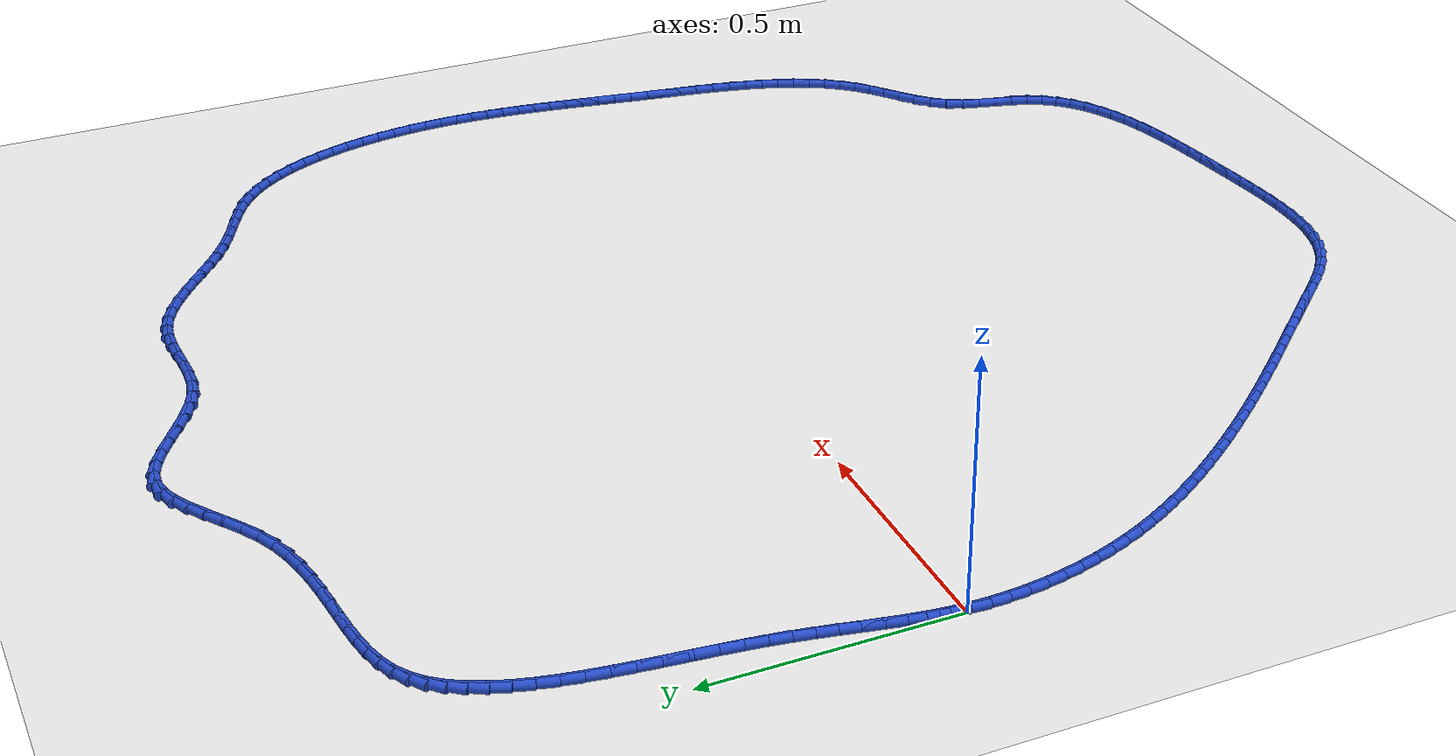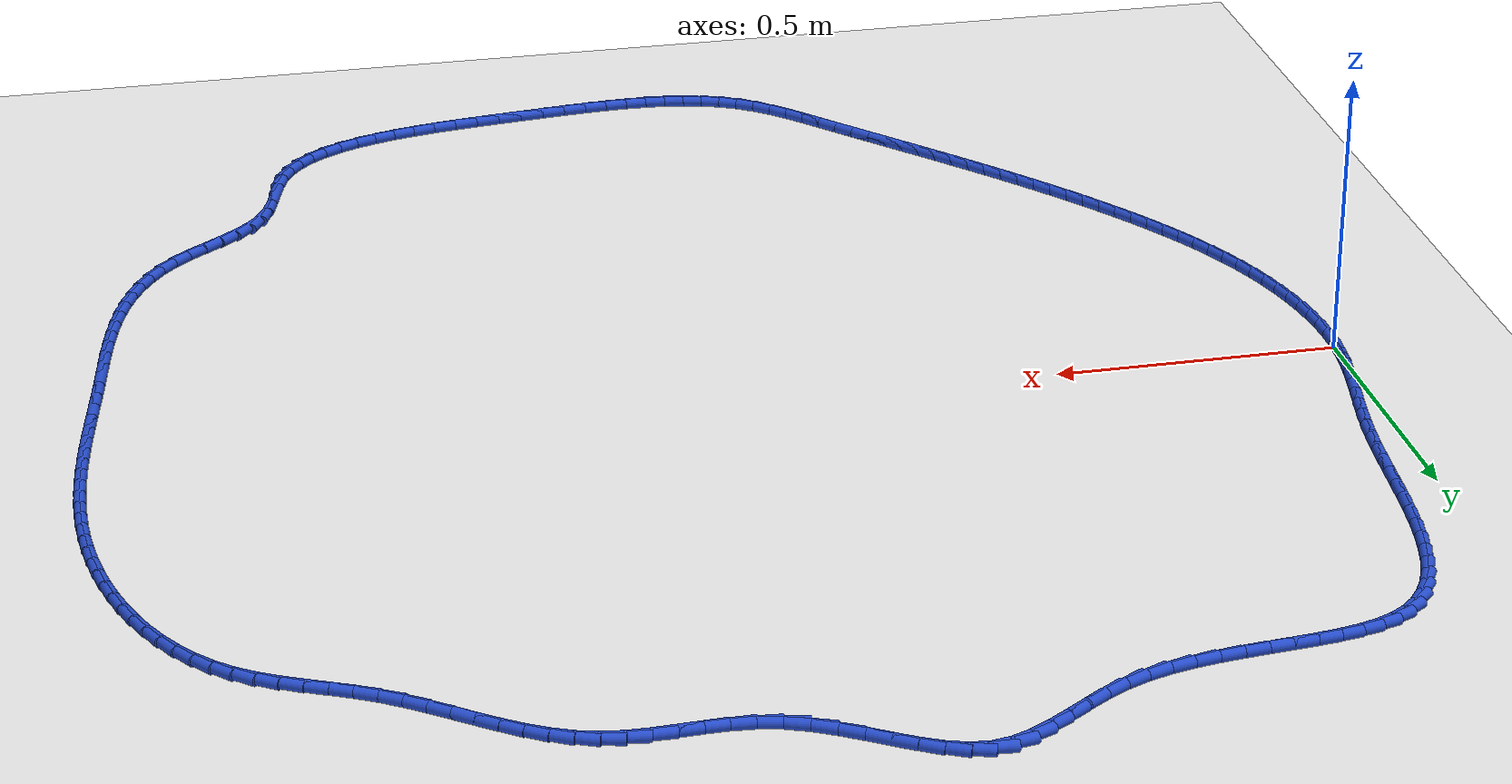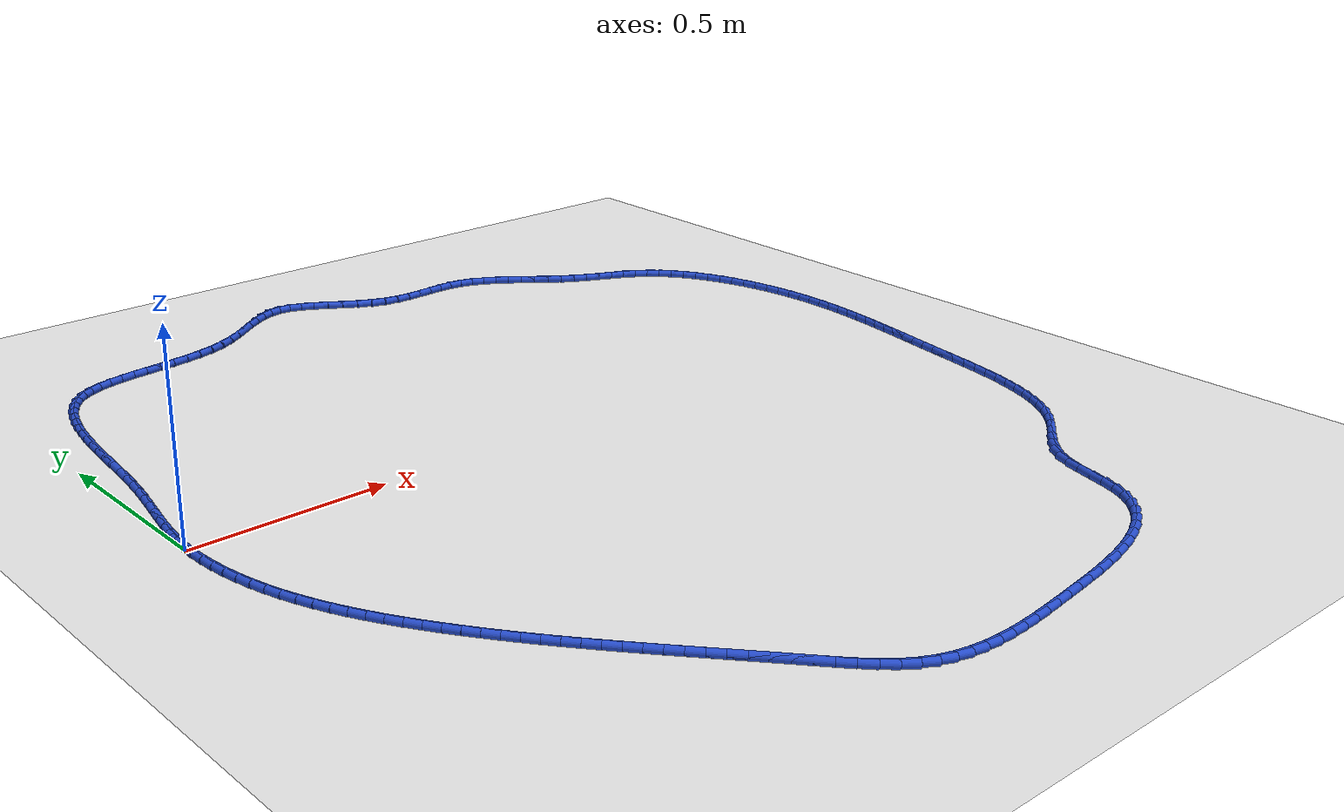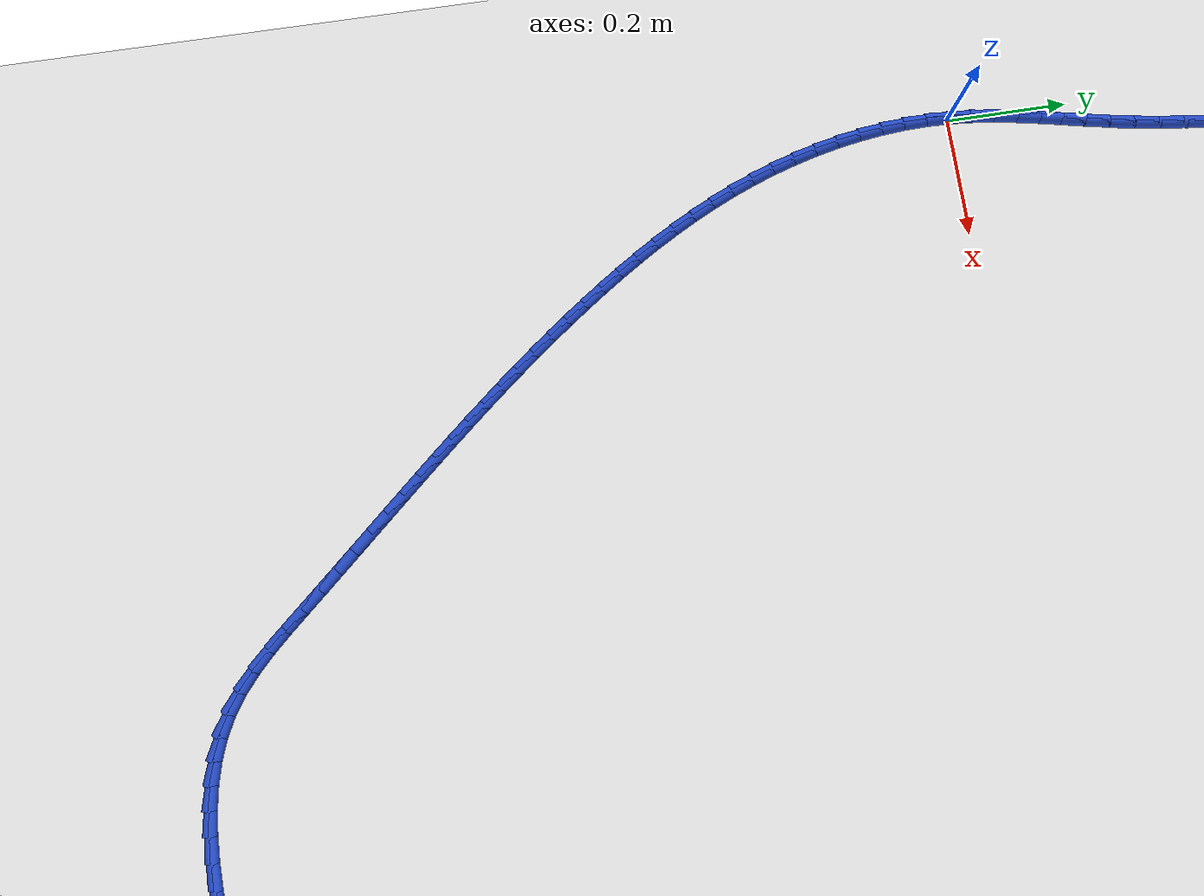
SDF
<sdf version="1.6">
 <world name="default">
  <light name="sun" type="directional">
   <pose>0 0 10 0 -0 0</pose>
   <diffuse>0.8 0.8 0.8 1</diffuse>
   <specular>0.2 0.2 0.2 1</specular>
   <attenuation>
    <range>1000</range>
    <constant>0.9</constant>
    <linear>0.01</linear>
    <quadratic>0.001</quadratic>
   </attenuation>
   <direction>-0.5 0.1 -0.9</direction>
  </light>
  <model name="ground_plane">
   <static>1</static>
   <link name="link">
    <collision name="collision">
     <geometry><plane><normal>0 0 1</normal><size>100 100</size></plane></geometry>
     <surface><friction><ode><mu>100</mu><mu2>50</mu2></ode></friction></surface>
    </collision>
    <visual name="visual">
     <cast_shadows>0</cast_shadows>
     <geometry><plane><normal>0 0 1</normal><size>100 100</size></plane></geometry>
     <material>
      <script><uri>file://media/materials/scripts/gazebo.material</uri><name>Gazebo/WhiteGlow</name></script>
     </material>
    </visual>
   </link>
  </model>
  <gravity>0 0 -9.8</gravity>
  <magnetic_field>6e-06 2.3e-05 -4.2e-05</magnetic_field>
  <atmosphere type="adiabatic"/>
  <physics name="default_physics" default="0" type="ode">
   <max_step_size>0.001</max_step_size>
   <real_time_factor>1</real_time_factor>
   <real_time_update_rate>1000</real_time_update_rate>
  </physics>
  <scene><ambient>0.4 0.4 0.4 1</ambient><background>0.7 0.7 0.7 1</background><shadows>1</shadows></scene>
  <spherical_coordinates>
   <surface_model>EARTH_WGS84</surface_model>
   <latitude_deg>0</latitude_deg>
   <longitude_deg>0</longitude_deg>
   <elevation>0</elevation>
   <heading_deg>0</heading_deg>
  </spherical_coordinates>
  <model name="line">
   <link name="link_0">
    <pose>1.214306433183765e-17 -5.551115123125783e-17 0.01 0 1.57 1.4960967762465893</pose>
    <collision name="collision">
     <geometry><cylinder><radius>0.01</radius><length>0.08</length></cylinder></geometry>
    </collision>
    <visual name="visual">
     <material>
      <script><name>Gazebo/Blue</name><uri>file://media/materials/scripts/gazebo.material</uri></script>
     </material>
     <geometry><cylinder><radius>0.01</radius><length>0.08</length></cylinder></geometry>
    </visual>
   </link>
   <link name="link_1">
    <pose>0.002791364216330285 0.037298354604954585 0.01 0 1.57 1.4484200430386638</pose>
    <collision name="collision">
     <geometry><cylinder><radius>0.01</radius><length>0.08</length></cylinder></geometry>
    </collision>
    <visual name="visual">
     <material>
      <script><name>Gazebo/Blue</name><uri>file://media/materials/scripts/gazebo.material</uri></script>
     </material>
     <geometry><cylinder><radius>0.01</radius><length>0.08</length></cylinder></geometry>
    </visual>
   </link>
   <link name="link_2">
    <pose>0.007340194656034385 0.0742834623729324 0.01 0 1.57 1.411404170414992</pose>
    <collision name="collision">
     <geometry><cylinder><radius>0.01</radius><length>0.08</length></cylinder></geometry>
    </collision>
    <visual name="visual">
     <material>
      <script><name>Gazebo/Blue</name><uri>file://media/materials/scripts/gazebo.material</uri></script>
     </material>
     <geometry><cylinder><radius>0.01</radius><length>0.08</length></cylinder></geometry>
    </visual>
   </link>
   <link name="link_3">
    <pose>0.013272829891203326 0.11118809328527089 0.01 0 1.57 1.3855890138664382</pose>
    <collision name="collision">
     <geometry><cylinder><radius>0.01</radius><length>0.08</length></cylinder></geometry>
    </collision>
    <visual name="visual">
     <material>
      <script><name>Gazebo/Blue</name><uri>file://media/materials/scripts/gazebo.material</uri></script>
     </material>
     <geometry><cylinder><radius>0.01</radius><length>0.08</length></cylinder></geometry>
    </visual>
   </link>
   <link name="link_4">
    <pose>0.020215608493928106 0.14824501732330728 0.01 0 1.57 1.3710684263856114</pose>
    <collision name="collision">
     <geometry><cylinder><radius>0.01</radius><length>0.08</length></cylinder></geometry>
    </collision>
    <visual name="visual">
     <material>
      <script><name>Gazebo/Blue</name><uri>file://media/materials/scripts/gazebo.material</uri></script>
     </material>
     <geometry><cylinder><radius>0.01</radius><length>0.08</length></cylinder></geometry>
    </visual>
   </link>
   <link name="link_5">
    <pose>0.027794869036299765 0.1856870044683791 0.01 0 1.57 1.3675939372295634</pose>
    <collision name="collision">
     <geometry><cylinder><radius>0.01</radius><length>0.08</length></cylinder></geometry>
    </collision>
    <visual name="visual">
     <material>
      <script><name>Gazebo/Blue</name><uri>file://media/materials/scripts/gazebo.material</uri></script>
     </material>
     <geometry><cylinder><radius>0.01</radius><length>0.08</length></cylinder></geometry>
    </visual>
   </link>
   <link name="link_6">
    <pose>0.0356369500904093 0.22374682470182364 0.01 0 1.57 1.3746575311386873</pose>
    <collision name="collision">
     <geometry><cylinder><radius>0.01</radius><length>0.08</length></cylinder></geometry>
    </collision>
    <visual name="visual">
     <material>
      <script><name>Gazebo/Blue</name><uri>file://media/materials/scripts/gazebo.material</uri></script>
     </material>
     <geometry><cylinder><radius>0.01</radius><length>0.08</length></cylinder></geometry>
    </visual>
   </link>
   <link name="link_7">
    <pose>0.04336819022834772 0.2626572480049783 0.01 0 1.57 1.3915446354443641</pose>
    <collision name="collision">
     <geometry><cylinder><radius>0.01</radius><length>0.08</length></cylinder></geometry>
    </collision>
    <visual name="visual">
     <material>
      <script><name>Gazebo/Blue</name><uri>file://media/materials/scripts/gazebo.material</uri></script>
     </material>
     <geometry><cylinder><radius>0.01</radius><length>0.08</length></cylinder></geometry>
    </visual>
   </link>
   <link name="link_8">
    <pose>0.05061492802220603 0.30265104435918044 0.01 0 1.57 1.4170676760448138</pose>
    <collision name="collision">
     <geometry><cylinder><radius>0.01</radius><length>0.08</length></cylinder></geometry>
    </collision>
    <visual name="visual">
     <material>
      <script><name>Gazebo/Blue</name><uri>file://media/materials/scripts/gazebo.material</uri></script>
     </material>
     <geometry><cylinder><radius>0.01</radius><length>0.08</length></cylinder></geometry>
    </visual>
   </link>
   <link name="link_9">
    <pose>0.05701441893428005 0.34395108369674005 0.01 0 1.57 1.4424523275774874</pose>
    <collision name="collision">
     <geometry><cylinder><radius>0.01</radius><length>0.08</length></cylinder></geometry>
    </collision>
    <visual name="visual">
     <material>
      <script><name>Gazebo/Blue</name><uri>file://media/materials/scripts/gazebo.material</uri></script>
     </material>
     <geometry><cylinder><radius>0.01</radius><length>0.08</length></cylinder></geometry>
    </visual>
   </link>
   <link name="link_10">
    <pose>0.06250627943232127 0.3865060380124679 0.01 0 1.57 1.4594717351525122</pose>
    <collision name="collision">
     <geometry><cylinder><radius>0.01</radius><length>0.08</length></cylinder></geometry>
    </collision>
    <visual name="visual">
     <material>
      <script><name>Gazebo/Blue</name><uri>file://media/materials/scripts/gazebo.material</uri></script>
     </material>
     <geometry><cylinder><radius>0.01</radius><length>0.08</length></cylinder></geometry>
    </visual>
   </link>
   <link name="link_11">
    <pose>0.06736405370102008 0.42996175489721356 0.01 0 1.57 1.468521504528391</pose>
    <collision name="collision">
     <geometry><cylinder><radius>0.01</radius><length>0.08</length></cylinder></geometry>
    </collision>
    <visual name="visual">
     <material>
      <script><name>Gazebo/Blue</name><uri>file://media/materials/scripts/gazebo.material</uri></script>
     </material>
     <geometry><cylinder><radius>0.01</radius><length>0.08</length></cylinder></geometry>
    </visual>
   </link>
   <link name="link_12">
    <pose>0.07187853568005004 0.47394843889542354 0.01 0 1.57 1.4700692810529499</pose>
    <collision name="collision">
     <geometry><cylinder><radius>0.01</radius><length>0.08</length></cylinder></geometry>
    </collision>
    <visual name="visual">
     <material>
      <script><name>Gazebo/Blue</name><uri>file://media/materials/scripts/gazebo.material</uri></script>
     </material>
     <geometry><cylinder><radius>0.01</radius><length>0.08</length></cylinder></geometry>
    </visual>
   </link>
   <link name="link_13">
    <pose>0.07634051930908475 0.518096294551545 0.01 0 1.57 1.4642293117819987</pose>
    <collision name="collision">
     <geometry><cylinder><radius>0.01</radius><length>0.08</length></cylinder></geometry>
    </collision>
    <visual name="visual">
     <material>
      <script><name>Gazebo/Blue</name><uri>file://media/materials/scripts/gazebo.material</uri></script>
     </material>
     <geometry><cylinder><radius>0.01</radius><length>0.08</length></cylinder></geometry>
    </visual>
   </link>
   <link name="link_14">
    <pose>0.08104079852779782 0.5620355264100243 0.01 0 1.57 1.4507747156640454</pose>
    <collision name="collision">
     <geometry><cylinder><radius>0.01</radius><length>0.08</length></cylinder></geometry>
    </collision>
    <visual name="visual">
     <material>
      <script><name>Gazebo/Blue</name><uri>file://media/materials/scripts/gazebo.material</uri></script>
     </material>
     <geometry><cylinder><radius>0.01</radius><length>0.08</length></cylinder></geometry>
    </visual>
   </link>
   <link name="link_15">
    <pose>0.08627016727586281 0.6053963390153083 0.01 0 1.57 1.4291231876510653</pose>
    <collision name="collision">
     <geometry><cylinder><radius>0.01</radius><length>0.08</length></cylinder></geometry>
    </collision>
    <visual name="visual">
     <material>
      <script><name>Gazebo/Blue</name><uri>file://media/materials/scripts/gazebo.material</uri></script>
     </material>
     <geometry><cylinder><radius>0.01</radius><length>0.08</length></cylinder></geometry>
    </visual>
   </link>
   <link name="link_16">
    <pose>0.0923194194929533 0.6478089369118436 0.01 0 1.57 1.398297414345846</pose>
    <collision name="collision">
     <geometry><cylinder><radius>0.01</radius><length>0.08</length></cylinder></geometry>
    </collision>
    <visual name="visual">
     <material>
      <script><name>Gazebo/Blue</name><uri>file://media/materials/scripts/gazebo.material</uri></script>
     </material>
     <geometry><cylinder><radius>0.01</radius><length>0.08</length></cylinder></geometry>
    </visual>
   </link>
   <link name="link_17">
    <pose>0.0994793491187429 0.688903524644077 0.01 0 1.57 1.3568638489832283</pose>
    <collision name="collision">
     <geometry><cylinder><radius>0.01</radius><length>0.08</length></cylinder></geometry>
    </collision>
    <visual name="visual">
     <material>
      <script><name>Gazebo/Blue</name><uri>file://media/materials/scripts/gazebo.material</uri></script>
     </material>
     <geometry><cylinder><radius>0.01</radius><length>0.08</length></cylinder></geometry>
    </visual>
   </link>
   <link name="link_18">
    <pose>0.10804075009290519 0.7283103067564553 0.01 0 1.57 1.3028622538094277</pose>
    <collision name="collision">
     <geometry><cylinder><radius>0.01</radius><length>0.08</length></cylinder></geometry>
    </collision>
    <visual name="visual">
     <material>
      <script><name>Gazebo/Blue</name><uri>file://media/materials/scripts/gazebo.material</uri></script>
     </material>
     <geometry><cylinder><radius>0.01</radius><length>0.08</length></cylinder></geometry>
    </visual>
   </link>
   <link name="link_19">
    <pose>0.11829441635511374 0.7656594877934251 0.01 0 1.57 1.2337618328190587</pose>
    <collision name="collision">
     <geometry><cylinder><radius>0.01</radius><length>0.08</length></cylinder></geometry>
    </collision>
    <visual name="visual">
     <material>
      <script><name>Gazebo/Blue</name><uri>file://media/materials/scripts/gazebo.material</uri></script>
     </material>
     <geometry><cylinder><radius>0.01</radius><length>0.08</length></cylinder></geometry>
    </visual>
   </link>
   <link name="link_20">
    <pose>0.13053114184504214 0.8005812722994328 0.01 0 1.57 1.1465321587797026</pose>
    <collision name="collision">
     <geometry><cylinder><radius>0.01</radius><length>0.08</length></cylinder></geometry>
    </collision>
    <visual name="visual">
     <material>
      <script><name>Gazebo/Blue</name><uri>file://media/materials/scripts/gazebo.material</uri></script>
     </material>
     <geometry><cylinder><radius>0.01</radius><length>0.08</length></cylinder></geometry>
    </visual>
   </link>
   <link name="link_21">
    <pose>0.14504172050236402 0.8327058648189257 0.01 0 1.57 1.038012299472994</pose>
    <collision name="collision">
     <geometry><cylinder><radius>0.01</radius><length>0.08</length></cylinder></geometry>
    </collision>
    <visual name="visual">
     <material>
      <script><name>Gazebo/Blue</name><uri>file://media/materials/scripts/gazebo.material</uri></script>
     </material>
     <geometry><cylinder><radius>0.01</radius><length>0.08</length></cylinder></geometry>
    </visual>
   </link>
   <link name="link_22">
    <pose>0.16211694626675288 0.8616634698963499 0.01 0 1.57 0.905869826898732</pose>
    <collision name="collision">
     <geometry><cylinder><radius>0.01</radius><length>0.08</length></cylinder></geometry>
    </collision>
    <visual name="visual">
     <material>
      <script><name>Gazebo/Blue</name><uri>file://media/materials/scripts/gazebo.material</uri></script>
     </material>
     <geometry><cylinder><radius>0.01</radius><length>0.08</length></cylinder></geometry>
    </visual>
   </link>
   <link name="link_23">
    <pose>0.18204761307788248 0.8870842920761528 0.01 0 1.57 0.7503683671335277</pose>
    <collision name="collision">
     <geometry><cylinder><radius>0.01</radius><length>0.08</length></cylinder></geometry>
    </collision>
    <visual name="visual">
     <material>
      <script><name>Gazebo/Blue</name><uri>file://media/materials/scripts/gazebo.material</uri></script>
     </material>
     <geometry><cylinder><radius>0.01</radius><length>0.08</length></cylinder></geometry>
    </visual>
   </link>
   <link name="link_24">
    <pose>0.2051245148754261 0.9085985359027803 0.01 0 1.57 0.5774066878984406</pose>
    <collision name="collision">
     <geometry><cylinder><radius>0.01</radius><length>0.08</length></cylinder></geometry>
    </collision>
    <visual name="visual">
     <material>
      <script><name>Gazebo/Blue</name><uri>file://media/materials/scripts/gazebo.material</uri></script>
     </material>
     <geometry><cylinder><radius>0.01</radius><length>0.08</length></cylinder></geometry>
    </visual>
   </link>
   <link name="link_25">
    <pose>0.2316224218690235 0.9258610809252307 0.01 0 1.57 0.41662880057526847</pose>
    <collision name="collision">
     <geometry><cylinder><radius>0.01</radius><length>0.08</length></cylinder></geometry>
    </collision>
    <visual name="visual">
     <material>
      <script><name>Gazebo/Blue</name><uri>file://media/materials/scripts/gazebo.material</uri></script>
     </material>
     <geometry><cylinder><radius>0.01</radius><length>0.08</length></cylinder></geometry>
    </visual>
   </link>
   <link name="link_26">
    <pose>0.2614650021485289 0.9390674702199784 0.01 0 1.57 0.2926085041157337</pose>
    <collision name="collision">
     <geometry><cylinder><radius>0.01</radius><length>0.08</length></cylinder></geometry>
    </collision>
    <visual name="visual">
     <material>
      <script><name>Gazebo/Blue</name><uri>file://media/materials/scripts/gazebo.material</uri></script>
     </material>
     <geometry><cylinder><radius>0.01</radius><length>0.08</length></cylinder></geometry>
    </visual>
   </link>
   <link name="link_27">
    <pose>0.29423424758872224 0.9489393954034439 0.01 0 1.57 0.20360929972111882</pose>
    <collision name="collision">
     <geometry><cylinder><radius>0.01</radius><length>0.08</length></cylinder></geometry>
    </collision>
    <visual name="visual">
     <material>
      <script><name>Gazebo/Blue</name><uri>file://media/materials/scripts/gazebo.material</uri></script>
     </material>
     <geometry><cylinder><radius>0.01</radius><length>0.08</length></cylinder></geometry>
    </visual>
   </link>
   <link name="link_28">
    <pose>0.32949801195296163 0.9562203194251234 0.01 0 1.57 0.1445499177189462</pose>
    <collision name="collision">
     <geometry><cylinder><radius>0.01</radius><length>0.08</length></cylinder></geometry>
    </collision>
    <visual name="visual">
     <material>
      <script><name>Gazebo/Blue</name><uri>file://media/materials/scripts/gazebo.material</uri></script>
     </material>
     <geometry><cylinder><radius>0.01</radius><length>0.08</length></cylinder></geometry>
    </visual>
   </link>
   <link name="link_29">
    <pose>0.366824149004605 0.961653705234513 0.01 0 1.57 0.11067815848307282</pose>
    <collision name="collision">
     <geometry><cylinder><radius>0.01</radius><length>0.08</length></cylinder></geometry>
    </collision>
    <visual name="visual">
     <material>
      <script><name>Gazebo/Blue</name><uri>file://media/materials/scripts/gazebo.material</uri></script>
     </material>
     <geometry><cylinder><radius>0.01</radius><length>0.08</length></cylinder></geometry>
    </visual>
   </link>
   <link name="link_30">
    <pose>0.4057805125070101 0.9659830157811089 0.01 0 1.57 0.09851588791789956</pose>
    <collision name="collision">
     <geometry><cylinder><radius>0.01</radius><length>0.08</length></cylinder></geometry>
    </collision>
    <visual name="visual">
     <material>
      <script><name>Gazebo/Blue</name><uri>file://media/materials/scripts/gazebo.material</uri></script>
     </material>
     <geometry><cylinder><radius>0.01</radius><length>0.08</length></cylinder></geometry>
    </visual>
   </link>
   <link name="link_31">
    <pose>0.4459349562235351 0.9699517140144069 0.01 0 1.57 0.10594369424999343</pose>
    <collision name="collision">
     <geometry><cylinder><radius>0.01</radius><length>0.08</length></cylinder></geometry>
    </collision>
    <visual name="visual">
     <material>
      <script><name>Gazebo/Blue</name><uri>file://media/materials/scripts/gazebo.material</uri></script>
     </material>
     <geometry><cylinder><radius>0.01</radius><length>0.08</length></cylinder></geometry>
    </visual>
   </link>
   <link name="link_32">
    <pose>0.4868553339175375 0.9743032628839029 0.01 0 1.57 0.13201102547973598</pose>
    <collision name="collision">
     <geometry><cylinder><radius>0.01</radius><length>0.08</length></cylinder></geometry>
    </collision>
    <visual name="visual">
     <material>
      <script><name>Gazebo/Blue</name><uri>file://media/materials/scripts/gazebo.material</uri></script>
     </material>
     <geometry><cylinder><radius>0.01</radius><length>0.08</length></cylinder></geometry>
    </visual>
   </link>
   <link name="link_33">
    <pose>0.5281094993523756 0.9797811253390936 0.01 0 1.57 0.1766708921187316</pose>
    <collision name="collision">
     <geometry><cylinder><radius>0.01</radius><length>0.08</length></cylinder></geometry>
    </collision>
    <visual name="visual">
     <material>
      <script><name>Gazebo/Blue</name><uri>file://media/materials/scripts/gazebo.material</uri></script>
     </material>
     <geometry><cylinder><radius>0.01</radius><length>0.08</length></cylinder></geometry>
    </visual>
   </link>
   <link name="link_34">
    <pose>0.5692653062914076 0.9871287643294749 0.01 0 1.57 0.24044559175090227</pose>
    <collision name="collision">
     <geometry><cylinder><radius>0.01</radius><length>0.08</length></cylinder></geometry>
    </collision>
    <visual name="visual">
     <material>
      <script><name>Gazebo/Blue</name><uri>file://media/materials/scripts/gazebo.material</uri></script>
     </material>
     <geometry><cylinder><radius>0.01</radius><length>0.08</length></cylinder></geometry>
    </visual>
   </link>
   <link name="link_35">
    <pose>0.6098906084979907 0.9970896428045426 0.01 0 1.57 0.3239431386012435</pose>
    <collision name="collision">
     <geometry><cylinder><radius>0.01</radius><length>0.08</length></cylinder></geometry>
    </collision>
    <visual name="visual">
     <material>
      <script><name>Gazebo/Blue</name><uri>file://media/materials/scripts/gazebo.material</uri></script>
     </material>
     <geometry><cylinder><radius>0.01</radius><length>0.08</length></cylinder></geometry>
    </visual>
   </link>
   <link name="link_36">
    <pose>0.6495532597354834 1.0104072237137927 0.01 0 1.57 0.42699493769528746</pose>
    <collision name="collision">
     <geometry><cylinder><radius>0.01</radius><length>0.08</length></cylinder></geometry>
    </collision>
    <visual name="visual">
     <material>
      <script><name>Gazebo/Blue</name><uri>file://media/materials/scripts/gazebo.material</uri></script>
     </material>
     <geometry><cylinder><radius>0.01</radius><length>0.08</length></cylinder></geometry>
    </visual>
   </link>
   <link name="link_37">
    <pose>0.6878226032099425 1.0278193498795178 0.01 0 1.57 0.5289797049309015</pose>
    <collision name="collision">
     <geometry><cylinder><radius>0.01</radius><length>0.08</length></cylinder></geometry>
    </collision>
    <visual name="visual">
     <material>
      <script><name>Gazebo/Blue</name><uri>file://media/materials/scripts/gazebo.material</uri></script>
     </material>
     <geometry><cylinder><radius>0.01</radius><length>0.08</length></cylinder></geometry>
    </visual>
   </link>
   <link name="link_38">
    <pose>0.724483791802886 1.0492495475820838 0.01 0 1.57 0.5917942028472519</pose>
    <collision name="collision">
     <geometry><cylinder><radius>0.01</radius><length>0.08</length></cylinder></geometry>
    </collision>
    <visual name="visual">
     <material>
      <script><name>Gazebo/Blue</name><uri>file://media/materials/scripts/gazebo.material</uri></script>
     </material>
     <geometry><cylinder><radius>0.01</radius><length>0.08</length></cylinder></geometry>
    </visual>
   </link>
   <link name="link_39">
    <pose>0.7597617642624124 1.0729618952328268 0.01 0 1.57 0.613378420275824</pose>
    <collision name="collision">
     <geometry><cylinder><radius>0.01</radius><length>0.08</length></cylinder></geometry>
    </collision>
    <visual name="visual">
     <material>
      <script><name>Gazebo/Blue</name><uri>file://media/materials/scripts/gazebo.material</uri></script>
     </material>
     <geometry><cylinder><radius>0.01</radius><length>0.08</length></cylinder></geometry>
    </visual>
   </link>
   <link name="link_40">
    <pose>0.7939349946215692 1.0970184660826658 0.01 0 1.57 0.5927945480074778</pose>
    <collision name="collision">
     <geometry><cylinder><radius>0.01</radius><length>0.08</length></cylinder></geometry>
    </collision>
    <visual name="visual">
     <material>
      <script><name>Gazebo/Blue</name><uri>file://media/materials/scripts/gazebo.material</uri></script>
     </material>
     <geometry><cylinder><radius>0.01</radius><length>0.08</length></cylinder></geometry>
    </visual>
   </link>
   <link name="link_41">
    <pose>0.8272819569134042 1.1194813333825184 0.01 0 1.57 0.5234759370524045</pose>
    <collision name="collision">
     <geometry><cylinder><radius>0.01</radius><length>0.08</length></cylinder></geometry>
    </collision>
    <visual name="visual">
     <material>
      <script><name>Gazebo/Blue</name><uri>file://media/materials/scripts/gazebo.material</uri></script>
     </material>
     <geometry><cylinder><radius>0.01</radius><length>0.08</length></cylinder></geometry>
    </visual>
   </link>
   <link name="link_42">
    <pose>0.8600811251709655 1.1384125703833032 0.01 0 1.57 0.39236778417497653</pose>
    <collision name="collision">
     <geometry><cylinder><radius>0.01</radius><length>0.08</length></cylinder></geometry>
    </collision>
    <visual name="visual">
     <material>
      <script><name>Gazebo/Blue</name><uri>file://media/materials/scripts/gazebo.material</uri></script>
     </material>
     <geometry><cylinder><radius>0.01</radius><length>0.08</length></cylinder></geometry>
    </visual>
   </link>
   <link name="link_43">
    <pose>0.8926109734273009 1.1518742503359383 0.01 0 1.57 0.18395617845024453</pose>
    <collision name="collision">
     <geometry><cylinder><radius>0.01</radius><length>0.08</length></cylinder></geometry>
    </collision>
    <visual name="visual">
     <material>
      <script><name>Gazebo/Blue</name><uri>file://media/materials/scripts/gazebo.material</uri></script>
     </material>
     <geometry><cylinder><radius>0.01</radius><length>0.08</length></cylinder></geometry>
    </visual>
   </link>
   <link name="link_44">
    <pose>0.9251499757154581 1.1579284464913413 0.01 0 1.57 -0.0884308134386021</pose>
    <collision name="collision">
     <geometry><cylinder><radius>0.01</radius><length>0.08</length></cylinder></geometry>
    </collision>
    <visual name="visual">
     <material>
      <script><name>Gazebo/Blue</name><uri>file://media/materials/scripts/gazebo.material</uri></script>
     </material>
     <geometry><cylinder><radius>0.01</radius><length>0.08</length></cylinder></geometry>
    </visual>
   </link>
   <link name="link_45">
    <pose>0.9579584021648121 1.1550195842541227 0.01 0 1.57 -0.3156413184015592</pose>
    <collision name="collision">
     <geometry><cylinder><radius>0.01</radius><length>0.08</length></cylinder></geometry>
    </collision>
    <visual name="visual">
     <material>
      <script><name>Gazebo/Blue</name><uri>file://media/materials/scripts/gazebo.material</uri></script>
     </material>
     <geometry><cylinder><radius>0.01</radius><length>0.08</length></cylinder></geometry>
    </visual>
   </link>
   <link name="link_46">
    <pose>0.9911736523076631 1.144172845237093 0.01 0 1.57 -0.45979049337486355</pose>
    <collision name="collision">
     <geometry><cylinder><radius>0.01</radius><length>0.08</length></cylinder></geometry>
    </collision>
    <visual name="visual">
     <material>
      <script><name>Gazebo/Blue</name><uri>file://media/materials/scripts/gazebo.material</uri></script>
     </material>
     <geometry><cylinder><radius>0.01</radius><length>0.08</length></cylinder></geometry>
    </visual>
   </link>
   <link name="link_47">
    <pose>1.024882310441322 1.1274807268819713 0.01 0 1.57 -0.5375951508171143</pose>
    <collision name="collision">
     <geometry><cylinder><radius>0.01</radius><length>0.08</length></cylinder></geometry>
    </collision>
    <visual name="visual">
     <material>
      <script><name>Gazebo/Blue</name><uri>file://media/materials/scripts/gazebo.material</uri></script>
     </material>
     <geometry><cylinder><radius>0.01</radius><length>0.08</length></cylinder></geometry>
    </visual>
   </link>
   <link name="link_48">
    <pose>1.0591707994439508 1.1070391170549077 0.01 0 1.57 -0.5636952013133198</pose>
    <collision name="collision">
     <geometry><cylinder><radius>0.01</radius><length>0.08</length></cylinder></geometry>
    </collision>
    <visual name="visual">
     <material>
      <script><name>Gazebo/Blue</name><uri>file://media/materials/scripts/gazebo.material</uri></script>
     </material>
     <geometry><cylinder><radius>0.01</radius><length>0.08</length></cylinder></geometry>
    </visual>
   </link>
   <link name="link_49">
    <pose>1.0941255421937102 1.0849439036220536 0.01 0 1.57 -0.5451110758940891</pose>
    <collision name="collision">
     <geometry><cylinder><radius>0.01</radius><length>0.08</length></cylinder></geometry>
    </collision>
    <visual name="visual">
     <material>
      <script><name>Gazebo/Blue</name><uri>file://media/materials/scripts/gazebo.material</uri></script>
     </material>
     <geometry><cylinder><radius>0.01</radius><length>0.08</length></cylinder></geometry>
    </visual>
   </link>
   <link name="link_50">
    <pose>1.1298329615687628 1.0632909744495607 0.01 0 1.57 -0.4818977836394871</pose>
    <collision name="collision">
     <geometry><cylinder><radius>0.01</radius><length>0.08</length></cylinder></geometry>
    </collision>
    <visual name="visual">
     <material>
      <script><name>Gazebo/Blue</name><uri>file://media/materials/scripts/gazebo.material</uri></script>
     </material>
     <geometry><cylinder><radius>0.01</radius><length>0.08</length></cylinder></geometry>
    </visual>
   </link>
   <link name="link_51">
    <pose>1.1663794804472691 1.0441762174035782 0.01 0 1.57 -0.36876237907054593</pose>
    <collision name="collision">
     <geometry><cylinder><radius>0.01</radius><length>0.08</length></cylinder></geometry>
    </collision>
    <visual name="visual">
     <material>
      <script><name>Gazebo/Blue</name><uri>file://media/materials/scripts/gazebo.material</uri></script>
     </material>
     <geometry><cylinder><radius>0.01</radius><length>0.08</length></cylinder></geometry>
    </visual>
   </link>
   <link name="link_52">
    <pose>1.203851521707391 1.0296955203502587 0.01 0 1.57 -0.21095598486523584</pose>
    <collision name="collision">
     <geometry><cylinder><radius>0.01</radius><length>0.08</length></cylinder></geometry>
    </collision>
    <visual name="visual">
     <material>
      <script><name>Gazebo/Blue</name><uri>file://media/materials/scripts/gazebo.material</uri></script>
     </material>
     <geometry><cylinder><radius>0.01</radius><length>0.08</length></cylinder></geometry>
    </visual>
   </link>
   <link name="link_53">
    <pose>1.2422780355674703 1.021466787385188 0.01 0 1.57 -0.075652017089533</pose>
    <collision name="collision">
     <geometry><cylinder><radius>0.01</radius><length>0.08</length></cylinder></geometry>
    </collision>
    <visual name="visual">
     <material>
      <script><name>Gazebo/Blue</name><uri>file://media/materials/scripts/gazebo.material</uri></script>
     </material>
     <geometry><cylinder><radius>0.01</radius><length>0.08</length></cylinder></geometry>
    </visual>
   </link>
   <link name="link_54">
    <pose>1.2813748029363758 1.0185033825001908 0.01 0 1.57 0.010983071330957342</pose>
    <collision name="collision">
     <geometry><cylinder><radius>0.01</radius><length>0.08</length></cylinder></geometry>
    </collision>
    <visual name="visual">
     <material>
      <script><name>Gazebo/Blue</name><uri>file://media/materials/scripts/gazebo.material</uri></script>
     </material>
     <geometry><cylinder><radius>0.01</radius><length>0.08</length></cylinder></geometry>
    </visual>
   </link>
   <link name="link_55">
    <pose>1.3207514578710802 1.0189358765005276 0.01 0 1.57 0.04983007580823879</pose>
    <collision name="collision">
     <geometry><cylinder><radius>0.01</radius><length>0.08</length></cylinder></geometry>
    </collision>
    <visual name="visual">
     <material>
      <script><name>Gazebo/Blue</name><uri>file://media/materials/scripts/gazebo.material</uri></script>
     </material>
     <geometry><cylinder><radius>0.01</radius><length>0.08</length></cylinder></geometry>
    </visual>
   </link>
   <link name="link_56">
    <pose>1.360017549019952 1.0208941298723706 0.01 0 1.57 0.04160811628697034</pose>
    <collision name="collision">
     <geometry><cylinder><radius>0.01</radius><length>0.08</length></cylinder></geometry>
    </collision>
    <visual name="visual">
     <material>
      <script><name>Gazebo/Blue</name><uri>file://media/materials/scripts/gazebo.material</uri></script>
     </material>
     <geometry><cylinder><radius>0.01</radius><length>0.08</length></cylinder></geometry>
    </visual>
   </link>
   <link name="link_57">
    <pose>1.398782625031359 1.0225080031018914 0.01 0 1.57 -0.015857904344158357</pose>
    <collision name="collision">
     <geometry><cylinder><radius>0.01</radius><length>0.08</length></cylinder></geometry>
    </collision>
    <visual name="visual">
     <material>
      <script><name>Gazebo/Blue</name><uri>file://media/materials/scripts/gazebo.material</uri></script>
     </material>
     <geometry><cylinder><radius>0.01</radius><length>0.08</length></cylinder></geometry>
    </visual>
   </link>
   <link name="link_58">
    <pose>1.43665623455367 1.0219073566752621 0.01 0 1.57 -0.12734291241009738</pose>
    <collision name="collision">
     <geometry><cylinder><radius>0.01</radius><length>0.08</length></cylinder></geometry>
    </collision>
    <visual name="visual">
     <material>
      <script><name>Gazebo/Blue</name><uri>file://media/materials/scripts/gazebo.material</uri></script>
     </material>
     <geometry><cylinder><radius>0.01</radius><length>0.08</length></cylinder></geometry>
    </visual>
   </link>
   <link name="link_59">
    <pose>1.4732479896399073 1.0172223039811588 0.01 0 1.57 -0.27898358138562007</pose>
    <collision name="collision">
     <geometry><cylinder><radius>0.01</radius><length>0.08</length></cylinder></geometry>
    </collision>
    <visual name="visual">
     <material>
      <script><name>Gazebo/Blue</name><uri>file://media/materials/scripts/gazebo.material</uri></script>
     </material>
     <geometry><cylinder><radius>0.01</radius><length>0.08</length></cylinder></geometry>
    </visual>
   </link>
   <link name="link_60">
    <pose>1.5083163868573801 1.007176814900471 0.01 0 1.57 -0.4134794339668781</pose>
    <collision name="collision">
     <geometry><cylinder><radius>0.01</radius><length>0.08</length></cylinder></geometry>
    </collision>
    <visual name="visual">
     <material>
      <script><name>Gazebo/Blue</name><uri>file://media/materials/scripts/gazebo.material</uri></script>
     </material>
     <geometry><cylinder><radius>0.01</radius><length>0.08</length></cylinder></geometry>
    </visual>
   </link>
   <link name="link_61">
    <pose>1.5420872819353577 0.9923590174091181 0.01 0 1.57 -0.5168349474370424</pose>
    <collision name="collision">
     <geometry><cylinder><radius>0.01</radius><length>0.08</length></cylinder></geometry>
    </collision>
    <visual name="visual">
     <material>
      <script><name>Gazebo/Blue</name><uri>file://media/materials/scripts/gazebo.material</uri></script>
     </material>
     <geometry><cylinder><radius>0.01</radius><length>0.08</length></cylinder></geometry>
    </visual>
   </link>
   <link name="link_62">
    <pose>1.5748779953306584 0.9737218653517401 0.01 0 1.57 -0.589831662318913</pose>
    <collision name="collision">
     <geometry><cylinder><radius>0.01</radius><length>0.08</length></cylinder></geometry>
    </collision>
    <visual name="visual">
     <material>
      <script><name>Gazebo/Blue</name><uri>file://media/materials/scripts/gazebo.material</uri></script>
     </material>
     <geometry><cylinder><radius>0.01</radius><length>0.08</length></cylinder></geometry>
    </visual>
   </link>
   <link name="link_63">
    <pose>1.6070058475000994 0.9522183125729768 0.01 0 1.57 -0.6349952165638123</pose>
    <collision name="collision">
     <geometry><cylinder><radius>0.01</radius><length>0.08</length></cylinder></geometry>
    </collision>
    <visual name="visual">
     <material>
      <script><name>Gazebo/Blue</name><uri>file://media/materials/scripts/gazebo.material</uri></script>
     </material>
     <geometry><cylinder><radius>0.01</radius><length>0.08</length></cylinder></geometry>
    </visual>
   </link>
   <link name="link_64">
    <pose>1.6387881589004993 0.9288013129174674 0.01 0 1.57 -0.654730766561439</pose>
    <collision name="collision">
     <geometry><cylinder><radius>0.01</radius><length>0.08</length></cylinder></geometry>
    </collision>
    <visual name="visual">
     <material>
      <script><name>Gazebo/Blue</name><uri>file://media/materials/scripts/gazebo.material</uri></script>
     </material>
     <geometry><cylinder><radius>0.01</radius><length>0.08</length></cylinder></geometry>
    </visual>
   </link>
   <link name="link_65">
    <pose>1.6705422499886748 0.9044238202298515 0.01 0 1.57 -0.6505072465358958</pose>
    <collision name="collision">
     <geometry><cylinder><radius>0.01</radius><length>0.08</length></cylinder></geometry>
    </collision>
    <visual name="visual">
     <material>
      <script><name>Gazebo/Blue</name><uri>file://media/materials/scripts/gazebo.material</uri></script>
     </material>
     <geometry><cylinder><radius>0.01</radius><length>0.08</length></cylinder></geometry>
    </visual>
   </link>
   <link name="link_66">
    <pose>1.7025854412214434 0.8800387883547691 0.01 0 1.57 -0.6226479556047881</pose>
    <collision name="collision">
     <geometry><cylinder><radius>0.01</radius><length>0.08</length></cylinder></geometry>
    </collision>
    <visual name="visual">
     <material>
      <script><name>Gazebo/Blue</name><uri>file://media/materials/scripts/gazebo.material</uri></script>
     </material>
     <geometry><cylinder><radius>0.01</radius><length>0.08</length></cylinder></geometry>
    </visual>
   </link>
   <link name="link_67">
    <pose>1.735235053055624 0.8565991711368596 0.01 0 1.57 -0.5704597942559396</pose>
    <collision name="collision">
     <geometry><cylinder><radius>0.01</radius><length>0.08</length></cylinder></geometry>
    </collision>
    <visual name="visual">
     <material>
      <script><name>Gazebo/Blue</name><uri>file://media/materials/scripts/gazebo.material</uri></script>
     </material>
     <geometry><cylinder><radius>0.01</radius><length>0.08</length></cylinder></geometry>
    </visual>
   </link>
   <link name="link_68">
    <pose>1.7688084059480333 0.8350579224207628 0.01 0 1.57 -0.4990698685989431</pose>
    <collision name="collision">
     <geometry><cylinder><radius>0.01</radius><length>0.08</length></cylinder></geometry>
    </collision>
    <visual name="visual">
     <material>
      <script><name>Gazebo/Blue</name><uri>file://media/materials/scripts/gazebo.material</uri></script>
     </material>
     <geometry><cylinder><radius>0.01</radius><length>0.08</length></cylinder></geometry>
    </visual>
   </link>
   <link name="link_69">
    <pose>1.803513753651474 0.8161401978272914 0.01 0 1.57 -0.4471915604072485</pose>
    <collision name="collision">
     <geometry><cylinder><radius>0.01</radius><length>0.08</length></cylinder></geometry>
    </collision>
    <visual name="visual">
     <material>
      <script><name>Gazebo/Blue</name><uri>file://media/materials/scripts/gazebo.material</uri></script>
     </material>
     <geometry><cylinder><radius>0.01</radius><length>0.08</length></cylinder></geometry>
    </visual>
   </link>
   <link name="link_70">
    <pose>1.8388902930908457 0.7991737516492257 0.01 0 1.57 -0.43028947240999915</pose>
    <collision name="collision">
     <geometry><cylinder><radius>0.01</radius><length>0.08</length></cylinder></geometry>
    </collision>
    <visual name="visual">
     <material>
      <script><name>Gazebo/Blue</name><uri>file://media/materials/scripts/gazebo.material</uri></script>
     </material>
     <geometry><cylinder><radius>0.01</radius><length>0.08</length></cylinder></geometry>
    </visual>
   </link>
   <link name="link_71">
    <pose>1.874223659609266 0.7829567459588548 0.01 0 1.57 -0.44926367710668574</pose>
    <collision name="collision">
     <geometry><cylinder><radius>0.01</radius><length>0.08</length></cylinder></geometry>
    </collision>
    <visual name="visual">
     <material>
      <script><name>Gazebo/Blue</name><uri>file://media/materials/scripts/gazebo.material</uri></script>
     </material>
     <geometry><cylinder><radius>0.01</radius><length>0.08</length></cylinder></geometry>
    </visual>
   </link>
   <link name="link_72">
    <pose>1.9087990070898724 0.7662863372445088 0.01 0 1.57 -0.5056288452672292</pose>
    <collision name="collision">
     <geometry><cylinder><radius>0.01</radius><length>0.08</length></cylinder></geometry>
    </collision>
    <visual name="visual">
     <material>
      <script><name>Gazebo/Blue</name><uri>file://media/materials/scripts/gazebo.material</uri></script>
     </material>
     <geometry><cylinder><radius>0.01</radius><length>0.08</length></cylinder></geometry>
    </visual>
   </link>
   <link name="link_73">
    <pose>1.9419014894158007 0.7479596819945177 0.01 0 1.57 -0.6004953922942099</pose>
    <collision name="collision">
     <geometry><cylinder><radius>0.01</radius><length>0.08</length></cylinder></geometry>
    </collision>
    <visual name="visual">
     <material>
      <script><name>Gazebo/Blue</name><uri>file://media/materials/scripts/gazebo.material</uri></script>
     </material>
     <geometry><cylinder><radius>0.01</radius><length>0.08</length></cylinder></geometry>
    </visual>
   </link>
   <link name="link_74">
    <pose>1.9728212673469605 0.7267838295471042 0.01 0 1.57 -0.7158110308946194</pose>
    <collision name="collision">
     <geometry><cylinder><radius>0.01</radius><length>0.08</length></cylinder></geometry>
    </collision>
    <visual name="visual">
     <material>
      <script><name>Gazebo/Blue</name><uri>file://media/materials/scripts/gazebo.material</uri></script>
     </material>
     <geometry><cylinder><radius>0.01</radius><length>0.08</length></cylinder></geometry>
    </visual>
   </link>
   <link name="link_75">
    <pose>2.0011448157784226 0.7021513022598448 0.01 0 1.57 -0.8231492777179116</pose>
    <collision name="collision">
     <geometry><cylinder><radius>0.01</radius><length>0.08</length></cylinder></geometry>
    </collision>
    <visual name="visual">
     <material>
      <script><name>Gazebo/Blue</name><uri>file://media/materials/scripts/gazebo.material</uri></script>
     </material>
     <geometry><cylinder><radius>0.01</radius><length>0.08</length></cylinder></geometry>
    </visual>
   </link>
   <link name="link_76">
    <pose>2.0269155552674945 0.6743574797110984 0.01 0 1.57 -0.919733079183258</pose>
    <collision name="collision">
     <geometry><cylinder><radius>0.01</radius><length>0.08</length></cylinder></geometry>
    </collision>
    <visual name="visual">
     <material>
      <script><name>Gazebo/Blue</name><uri>file://media/materials/scripts/gazebo.material</uri></script>
     </material>
     <geometry><cylinder><radius>0.01</radius><length>0.08</length></cylinder></geometry>
    </visual>
   </link>
   <link name="link_77">
    <pose>2.050215941154951 0.6437748684530051 0.01 0 1.57 -1.005941736891699</pose>
    <collision name="collision">
     <geometry><cylinder><radius>0.01</radius><length>0.08</length></cylinder></geometry>
    </collision>
    <visual name="visual">
     <material>
      <script><name>Gazebo/Blue</name><uri>file://media/materials/scripts/gazebo.material</uri></script>
     </material>
     <geometry><cylinder><radius>0.01</radius><length>0.08</length></cylinder></geometry>
    </visual>
   </link>
   <link name="link_78">
    <pose>2.0711284287815634 0.6107759750377052 0.01 0 1.57 -1.0826710046783337</pose>
    <collision name="collision">
     <geometry><cylinder><radius>0.01</radius><length>0.08</length></cylinder></geometry>
    </collision>
    <visual name="visual">
     <material>
      <script><name>Gazebo/Blue</name><uri>file://media/materials/scripts/gazebo.material</uri></script>
     </material>
     <geometry><cylinder><radius>0.01</radius><length>0.08</length></cylinder></geometry>
    </visual>
   </link>
   <link name="link_79">
    <pose>2.0897354734881044 0.5757333060173389 0.01 0 1.57 -1.1510547761441032</pose>
    <collision name="collision">
     <geometry><cylinder><radius>0.01</radius><length>0.08</length></cylinder></geometry>
    </collision>
    <visual name="visual">
     <material>
      <script><name>Gazebo/Blue</name><uri>file://media/materials/scripts/gazebo.material</uri></script>
     </material>
     <geometry><cylinder><radius>0.01</radius><length>0.08</length></cylinder></geometry>
    </visual>
   </link>
   <link name="link_80">
    <pose>2.106119530615346 0.5390193679440467 0.01 0 1.57 -1.2122848672200714</pose>
    <collision name="collision">
     <geometry><cylinder><radius>0.01</radius><length>0.08</length></cylinder></geometry>
    </collision>
    <visual name="visual">
     <material>
      <script><name>Gazebo/Blue</name><uri>file://media/materials/scripts/gazebo.material</uri></script>
     </material>
     <geometry><cylinder><radius>0.01</radius><length>0.08</length></cylinder></geometry>
    </visual>
   </link>
   <link name="link_81">
    <pose>2.120363055504062 0.5010066673699684 0.01 0 1.57 -1.2675132056081804</pose>
    <collision name="collision">
     <geometry><cylinder><radius>0.01</radius><length>0.08</length></cylinder></geometry>
    </collision>
    <visual name="visual">
     <material>
      <script><name>Gazebo/Blue</name><uri>file://media/materials/scripts/gazebo.material</uri></script>
     </material>
     <geometry><cylinder><radius>0.01</radius><length>0.08</length></cylinder></geometry>
    </visual>
   </link>
   <link name="link_82">
    <pose>2.132548503495024 0.46206771084724463 0.01 0 1.57 -1.3178109694370566</pose>
    <collision name="collision">
     <geometry><cylinder><radius>0.01</radius><length>0.08</length></cylinder></geometry>
    </collision>
    <visual name="visual">
     <material>
      <script><name>Gazebo/Blue</name><uri>file://media/materials/scripts/gazebo.material</uri></script>
     </material>
     <geometry><cylinder><radius>0.01</radius><length>0.08</length></cylinder></geometry>
    </visual>
   </link>
   <link name="link_83">
    <pose>2.142758329929003 0.4225750049280156 0.01 0 1.57 -1.3641631103957979</pose>
    <collision name="collision">
     <geometry><cylinder><radius>0.01</radius><length>0.08</length></cylinder></geometry>
    </collision>
    <visual name="visual">
     <material>
      <script><name>Gazebo/Blue</name><uri>file://media/materials/scripts/gazebo.material</uri></script>
     </material>
     <geometry><cylinder><radius>0.01</radius><length>0.08</length></cylinder></geometry>
    </visual>
   </link>
   <link name="link_84">
    <pose>2.1510749901467747 0.3829010561644212 0.01 0 1.57 -1.4074950535915736</pose>
    <collision name="collision">
     <geometry><cylinder><radius>0.01</radius><length>0.08</length></cylinder></geometry>
    </collision>
    <visual name="visual">
     <material>
      <script><name>Gazebo/Blue</name><uri>file://media/materials/scripts/gazebo.material</uri></script>
     </material>
     <geometry><cylinder><radius>0.01</radius><length>0.08</length></cylinder></geometry>
    </visual>
   </link>
   <link name="link_85">
    <pose>2.15758147795195 0.34341239964667186 0.01 0 1.57 -1.448814769078173</pose>
    <collision name="collision">
     <geometry><cylinder><radius>0.01</radius><length>0.08</length></cylinder></geometry>
    </collision>
    <visual name="visual">
     <material>
      <script><name>Gazebo/Blue</name><uri>file://media/materials/scripts/gazebo.material</uri></script>
     </material>
     <geometry><cylinder><radius>0.01</radius><length>0.08</length></cylinder></geometry>
    </visual>
   </link>
   <link name="link_86">
    <pose>2.162377576819061 0.30428937585121263 0.01 0 1.57 -1.4883659673567584</pose>
    <collision name="collision">
     <geometry><cylinder><radius>0.01</radius><length>0.08</length></cylinder></geometry>
    </collision>
    <visual name="visual">
     <material>
      <script><name>Gazebo/Blue</name><uri>file://media/materials/scripts/gazebo.material</uri></script>
     </material>
     <geometry><cylinder><radius>0.01</radius><length>0.08</length></cylinder></geometry>
    </visual>
   </link>
   <link name="link_87">
    <pose>2.1655827472355593 0.26549411050572175 0.01 0 1.57 -1.5257872405074548</pose>
    <collision name="collision">
     <geometry><cylinder><radius>0.01</radius><length>0.08</length></cylinder></geometry>
    </collision>
    <visual name="visual">
     <material>
      <script><name>Gazebo/Blue</name><uri>file://media/materials/scripts/gazebo.material</uri></script>
     </material>
     <geometry><cylinder><radius>0.01</radius><length>0.08</length></cylinder></geometry>
    </visual>
   </link>
   <link name="link_88">
    <pose>2.167317570182435 0.22697630325386206 0.01 0 1.57 -1.5607405172393596</pose>
    <collision name="collision">
     <geometry><cylinder><radius>0.01</radius><length>0.08</length></cylinder></geometry>
    </collision>
    <visual name="visual">
     <material>
      <script><name>Gazebo/Blue</name><uri>file://media/materials/scripts/gazebo.material</uri></script>
     </material>
     <geometry><cylinder><radius>0.01</radius><length>0.08</length></cylinder></geometry>
    </visual>
   </link>
   <link name="link_89">
    <pose>2.1677026266406796 0.18868565373929555 0.01 0 1.57 1.5486523462803707</pose>
    <collision name="collision">
     <geometry><cylinder><radius>0.01</radius><length>0.08</length></cylinder></geometry>
    </collision>
    <visual name="visual">
     <material>
      <script><name>Gazebo/Blue</name><uri>file://media/materials/scripts/gazebo.material</uri></script>
     </material>
     <geometry><cylinder><radius>0.01</radius><length>0.08</length></cylinder></geometry>
    </visual>
   </link>
   <link name="link_90">
    <pose>2.166858497591282 0.15057186160568453 0.01 0 1.57 1.5194365403591128</pose>
    <collision name="collision">
     <geometry><cylinder><radius>0.01</radius><length>0.08</length></cylinder></geometry>
    </collision>
    <visual name="visual">
     <material>
      <script><name>Gazebo/Blue</name><uri>file://media/materials/scripts/gazebo.material</uri></script>
     </material>
     <geometry><cylinder><radius>0.01</radius><length>0.08</length></cylinder></geometry>
    </visual>
   </link>
   <link name="link_91">
    <pose>2.164905764015232 0.11258462649669031 0.01 0 1.57 1.4933812836000135</pose>
    <collision name="collision">
     <geometry><cylinder><radius>0.01</radius><length>0.08</length></cylinder></geometry>
    </collision>
    <visual name="visual">
     <material>
      <script><name>Gazebo/Blue</name><uri>file://media/materials/scripts/gazebo.material</uri></script>
     </material>
     <geometry><cylinder><radius>0.01</radius><length>0.08</length></cylinder></geometry>
    </visual>
   </link>
   <link name="link_92">
    <pose>2.1619650068935203 0.07467364805597547 0.01 0 1.57 1.4706129209182874</pose>
    <collision name="collision">
     <geometry><cylinder><radius>0.01</radius><length>0.08</length></cylinder></geometry>
    </collision>
    <visual name="visual">
     <material>
      <script><name>Gazebo/Blue</name><uri>file://media/materials/scripts/gazebo.material</uri></script>
     </material>
     <geometry><cylinder><radius>0.01</radius><length>0.08</length></cylinder></geometry>
    </visual>
   </link>
   <link name="link_93">
    <pose>2.1581568072071367 0.03678862592720244 0.01 0 1.57 1.4512130078775365</pose>
    <collision name="collision">
     <geometry><cylinder><radius>0.01</radius><length>0.08</length></cylinder></geometry>
    </collision>
    <visual name="visual">
     <material>
      <script><name>Gazebo/Blue</name><uri>file://media/materials/scripts/gazebo.material</uri></script>
     </material>
     <geometry><cylinder><radius>0.01</radius><length>0.08</length></cylinder></geometry>
    </visual>
   </link>
   <link name="link_94">
    <pose>2.1536017459370718 -0.00112074024596754 0.01 0 1.57 1.4352245693179695</pose>
    <collision name="collision">
     <geometry><cylinder><radius>0.01</radius><length>0.08</length></cylinder></geometry>
    </collision>
    <visual name="visual">
     <material>
      <script><name>Gazebo/Blue</name><uri>file://media/materials/scripts/gazebo.material</uri></script>
     </material>
     <geometry><cylinder><radius>0.01</radius><length>0.08</length></cylinder></geometry>
    </visual>
   </link>
   <link name="link_95">
    <pose>2.1484204040643142 -0.039104750819872 0.01 0 1.57 1.4226584399362203</pose>
    <collision name="collision">
     <geometry><cylinder><radius>0.01</radius><length>0.08</length></cylinder></geometry>
    </collision>
    <visual name="visual">
     <material>
      <script><name>Gazebo/Blue</name><uri>file://media/materials/scripts/gazebo.material</uri></script>
     </material>
     <geometry><cylinder><radius>0.01</radius><length>0.08</length></cylinder></geometry>
    </visual>
   </link>
   <link name="link_96">
    <pose>2.1427333625698557 -0.07721370615084877 0.01 0 1.57 1.4134991308408238</pose>
    <collision name="collision">
     <geometry><cylinder><radius>0.01</radius><length>0.08</length></cylinder></geometry>
    </collision>
    <visual name="visual">
     <material>
      <script><name>Gazebo/Blue</name><uri>file://media/materials/scripts/gazebo.material</uri></script>
     </material>
     <geometry><cylinder><radius>0.01</radius><length>0.08</length></cylinder></geometry>
    </visual>
   </link>
   <link name="link_97">
    <pose>2.136661202434686 -0.11549790659523594 0.01 0 1.57 1.407709858329337</pose>
    <collision name="collision">
     <geometry><cylinder><radius>0.01</radius><length>0.08</length></cylinder></geometry>
    </collision>
    <visual name="visual">
     <material>
      <script><name>Gazebo/Blue</name><uri>file://media/materials/scripts/gazebo.material</uri></script>
     </material>
     <geometry><cylinder><radius>0.01</radius><length>0.08</length></cylinder></geometry>
    </visual>
   </link>
   <link name="link_98">
    <pose>2.1303245046397947 -0.15400765250937049 0.01 0 1.57 1.4052365395207636</pose>
    <collision name="collision">
     <geometry><cylinder><radius>0.01</radius><length>0.08</length></cylinder></geometry>
    </collision>
    <visual name="visual">
     <material>
      <script><name>Gazebo/Blue</name><uri>file://media/materials/scripts/gazebo.material</uri></script>
     </material>
     <geometry><cylinder><radius>0.01</radius><length>0.08</length></cylinder></geometry>
    </visual>
   </link>
   <link name="link_99">
    <pose>2.1238438501661716 -0.192793244249592 0.01 0 1.57 1.4060106931762275</pose>
    <collision name="collision">
     <geometry><cylinder><radius>0.01</radius><length>0.08</length></cylinder></geometry>
    </collision>
    <visual name="visual">
     <material>
      <script><name>Gazebo/Blue</name><uri>file://media/materials/scripts/gazebo.material</uri></script>
     </material>
     <geometry><cylinder><radius>0.01</radius><length>0.08</length></cylinder></geometry>
    </visual>
   </link>
   <link name="link_100">
    <pose>2.1173398199948075 -0.2319049821722376 0.01 0 1.57 1.4099512828807024</pose>
    <collision name="collision">
     <geometry><cylinder><radius>0.01</radius><length>0.08</length></cylinder></geometry>
    </collision>
    <visual name="visual">
     <material>
      <script><name>Gazebo/Blue</name><uri>file://media/materials/scripts/gazebo.material</uri></script>
     </material>
     <geometry><cylinder><radius>0.01</radius><length>0.08</length></cylinder></geometry>
    </visual>
   </link>
   <link name="link_101">
    <pose>2.110932995106692 -0.27139316663364527 0.01 0 1.57 1.4157534463300914</pose>
    <collision name="collision">
     <geometry><cylinder><radius>0.01</radius><length>0.08</length></cylinder></geometry>
    </collision>
    <visual name="visual">
     <material>
      <script><name>Gazebo/Blue</name><uri>file://media/materials/scripts/gazebo.material</uri></script>
     </material>
     <geometry><cylinder><radius>0.01</radius><length>0.08</length></cylinder></geometry>
    </visual>
   </link>
   <link name="link_102">
    <pose>2.1046990493926594 -0.3112783540144613 0.01 0 1.57 1.4163641332261079</pose>
    <collision name="collision">
     <geometry><cylinder><radius>0.01</radius><length>0.08</length></cylinder></geometry>
    </collision>
    <visual name="visual">
     <material>
      <script><name>Gazebo/Blue</name><uri>file://media/materials/scripts/gazebo.material</uri></script>
     </material>
     <geometry><cylinder><radius>0.01</radius><length>0.08</length></cylinder></geometry>
    </visual>
   </link>
   <link name="link_103">
    <pose>2.098452027652399 -0.3514078120386868 0.01 0 1.57 1.4093453450265125</pose>
    <collision name="collision">
     <geometry><cylinder><radius>0.01</radius><length>0.08</length></cylinder></geometry>
    </collision>
    <visual name="visual">
     <material>
      <script><name>Gazebo/Blue</name><uri>file://media/materials/scripts/gazebo.material</uri></script>
     </material>
     <geometry><cylinder><radius>0.01</radius><length>0.08</length></cylinder></geometry>
    </visual>
   </link>
   <link name="link_104">
    <pose>2.091911484230375 -0.3915662231727708 0.01 0 1.57 1.3946502730597423</pose>
    <collision name="collision">
     <geometry><cylinder><radius>0.01</radius><length>0.08</length></cylinder></geometry>
    </collision>
    <visual name="visual">
     <material>
      <script><name>Gazebo/Blue</name><uri>file://media/materials/scripts/gazebo.material</uri></script>
     </material>
     <geometry><cylinder><radius>0.01</radius><length>0.08</length></cylinder></geometry>
    </visual>
   </link>
   <link name="link_105">
    <pose>2.0847968452516876 -0.4315381849577385 0.01 0 1.57 1.3720576899919326</pose>
    <collision name="collision">
     <geometry><cylinder><radius>0.01</radius><length>0.08</length></cylinder></geometry>
    </collision>
    <visual name="visual">
     <material>
      <script><name>Gazebo/Blue</name><uri>file://media/materials/scripts/gazebo.material</uri></script>
     </material>
     <geometry><cylinder><radius>0.01</radius><length>0.08</length></cylinder></geometry>
    </visual>
   </link>
   <link name="link_106">
    <pose>2.0768275368414364 -0.4711082949346177 0.01 0 1.57 1.3411857885740945</pose>
    <collision name="collision">
     <geometry><cylinder><radius>0.01</radius><length>0.08</length></cylinder></geometry>
    </collision>
    <visual name="visual">
     <material>
      <script><name>Gazebo/Blue</name><uri>file://media/materials/scripts/gazebo.material</uri></script>
     </material>
     <geometry><cylinder><radius>0.01</radius><length>0.08</length></cylinder></geometry>
    </visual>
   </link>
   <link name="link_107">
    <pose>2.067722985124721 -0.5100611506444337 0.01 0 1.57 1.3015203093908239</pose>
    <collision name="collision">
     <geometry><cylinder><radius>0.01</radius><length>0.08</length></cylinder></geometry>
    </collision>
    <visual name="visual">
     <material>
      <script><name>Gazebo/Blue</name><uri>file://media/materials/scripts/gazebo.material</uri></script>
     </material>
     <geometry><cylinder><radius>0.01</radius><length>0.08</length></cylinder></geometry>
    </visual>
   </link>
   <link name="link_108">
    <pose>2.0572026162266432 -0.5481813496282127 0.01 0 1.57 1.2524634782000443</pose>
    <collision name="collision">
     <geometry><cylinder><radius>0.01</radius><length>0.08</length></cylinder></geometry>
    </collision>
    <visual name="visual">
     <material>
      <script><name>Gazebo/Blue</name><uri>file://media/materials/scripts/gazebo.material</uri></script>
     </material>
     <geometry><cylinder><radius>0.01</radius><length>0.08</length></cylinder></geometry>
    </visual>
   </link>
   <link name="link_109">
    <pose>2.0449858562723016 -0.5852534894269807 0.01 0 1.57 1.193417400572968</pose>
    <collision name="collision">
     <geometry><cylinder><radius>0.01</radius><length>0.08</length></cylinder></geometry>
    </collision>
    <visual name="visual">
     <material>
      <script><name>Gazebo/Blue</name><uri>file://media/materials/scripts/gazebo.material</uri></script>
     </material>
     <geometry><cylinder><radius>0.01</radius><length>0.08</length></cylinder></geometry>
    </visual>
   </link>
   <link name="link_110">
    <pose>2.030792131386796 -0.6210621675817639 0.01 0 1.57 1.1239168759637137</pose>
    <collision name="collision">
     <geometry><cylinder><radius>0.01</radius><length>0.08</length></cylinder></geometry>
    </collision>
    <visual name="visual">
     <material>
      <script><name>Gazebo/Blue</name><uri>file://media/materials/scripts/gazebo.material</uri></script>
     </material>
     <geometry><cylinder><radius>0.01</radius><length>0.08</length></cylinder></geometry>
    </visual>
   </link>
   <link name="link_111">
    <pose>2.014340867695228 -0.6553919816335887 0.01 0 1.57 1.0438205597238692</pose>
    <collision name="collision">
     <geometry><cylinder><radius>0.01</radius><length>0.08</length></cylinder></geometry>
    </collision>
    <visual name="visual">
     <material>
      <script><name>Gazebo/Blue</name><uri>file://media/materials/scripts/gazebo.material</uri></script>
     </material>
     <geometry><cylinder><radius>0.01</radius><length>0.08</length></cylinder></geometry>
    </visual>
   </link>
   <link name="link_112">
    <pose>1.9953514913226962 -0.68802752912348 0.01 0 1.57 0.9535486442471789</pose>
    <collision name="collision">
     <geometry><cylinder><radius>0.01</radius><length>0.08</length></cylinder></geometry>
    </collision>
    <visual name="visual">
     <material>
      <script><name>Gazebo/Blue</name><uri>file://media/materials/scripts/gazebo.material</uri></script>
     </material>
     <geometry><cylinder><radius>0.01</radius><length>0.08</length></cylinder></geometry>
    </visual>
   </link>
   <link name="link_113">
    <pose>1.9735434283943016 -0.718753407592466 0.01 0 1.57 0.85431543339839</pose>
    <collision name="collision">
     <geometry><cylinder><radius>0.01</radius><length>0.08</length></cylinder></geometry>
    </collision>
    <visual name="visual">
     <material>
      <script><name>Gazebo/Blue</name><uri>file://media/materials/scripts/gazebo.material</uri></script>
     </material>
     <geometry><cylinder><radius>0.01</radius><length>0.08</length></cylinder></geometry>
    </visual>
   </link>
   <link name="link_114">
    <pose>1.948636105035143 -0.7473542145815713 0.01 0 1.57 0.7507832722630146</pose>
    <collision name="collision">
     <geometry><cylinder><radius>0.01</radius><length>0.08</length></cylinder></geometry>
    </collision>
    <visual name="visual">
     <material>
      <script><name>Gazebo/Blue</name><uri>file://media/materials/scripts/gazebo.material</uri></script>
     </material>
     <geometry><cylinder><radius>0.01</radius><length>0.08</length></cylinder></geometry>
    </visual>
   </link>
   <link name="link_115">
    <pose>1.9204306006758038 -0.7736716588637779 0.01 0 1.57 0.6779471716496512</pose>
    <collision name="collision">
     <geometry><cylinder><radius>0.01</radius><length>0.08</length></cylinder></geometry>
    </collision>
    <visual name="visual">
     <material>
      <script><name>Gazebo/Blue</name><uri>file://media/materials/scripts/gazebo.material</uri></script>
     </material>
     <geometry><cylinder><radius>0.01</radius><length>0.08</length></cylinder></geometry>
    </visual>
   </link>
   <link name="link_116">
    <pose>1.8898268281888364 -0.7983160124834981 0.01 0 1.57 0.6565695907384311</pose>
    <collision name="collision">
     <geometry><cylinder><radius>0.01</radius><length>0.08</length></cylinder></geometry>
    </collision>
    <visual name="visual">
     <material>
      <script><name>Gazebo/Blue</name><uri>file://media/materials/scripts/gazebo.material</uri></script>
     </material>
     <geometry><cylinder><radius>0.01</radius><length>0.08</length></cylinder></geometry>
    </visual>
   </link>
   <link name="link_117">
    <pose>1.858511809860532 -0.8224480798614734 0.01 0 1.57 0.6854046236780491</pose>
    <collision name="collision">
     <geometry><cylinder><radius>0.01</radius><length>0.08</length></cylinder></geometry>
    </collision>
    <visual name="visual">
     <material>
      <script><name>Gazebo/Blue</name><uri>file://media/materials/scripts/gazebo.material</uri></script>
     </material>
     <geometry><cylinder><radius>0.01</radius><length>0.08</length></cylinder></geometry>
    </visual>
   </link>
   <link name="link_118">
    <pose>1.8281896928328079 -0.847240643152794 0.01 0 1.57 0.7669816196945624</pose>
    <collision name="collision">
     <geometry><cylinder><radius>0.01</radius><length>0.08</length></cylinder></geometry>
    </collision>
    <visual name="visual">
     <material>
      <script><name>Gazebo/Blue</name><uri>file://media/materials/scripts/gazebo.material</uri></script>
     </material>
     <geometry><cylinder><radius>0.01</radius><length>0.08</length></cylinder></geometry>
    </visual>
   </link>
   <link name="link_119">
    <pose>1.8005646242475795 -0.8738664845125512 0.01 0 1.57 0.9060454748563066</pose>
    <collision name="collision">
     <geometry><cylinder><radius>0.01</radius><length>0.08</length></cylinder></geometry>
    </collision>
    <visual name="visual">
     <material>
      <script><name>Gazebo/Blue</name><uri>file://media/materials/scripts/gazebo.material</uri></script>
     </material>
     <geometry><cylinder><radius>0.01</radius><length>0.08</length></cylinder></geometry>
    </visual>
   </link>
   <link name="link_120">
    <pose>1.7773407512467643 -0.9034983860958358 0.01 0 1.57 1.0924008980881115</pose>
    <collision name="collision">
     <geometry><cylinder><radius>0.01</radius><length>0.08</length></cylinder></geometry>
    </collision>
    <visual name="visual">
     <material>
      <script><name>Gazebo/Blue</name><uri>file://media/materials/scripts/gazebo.material</uri></script>
     </material>
     <geometry><cylinder><radius>0.01</radius><length>0.08</length></cylinder></geometry>
    </visual>
   </link>
   <link name="link_121">
    <pose>1.7599205660133777 -0.9370909229879482 0.01 0 1.57 1.238586335258625</pose>
    <collision name="collision">
     <geometry><cylinder><radius>0.01</radius><length>0.08</length></cylinder></geometry>
    </collision>
    <visual name="visual">
     <material>
      <script><name>Gazebo/Blue</name><uri>file://media/materials/scripts/gazebo.material</uri></script>
     </material>
     <geometry><cylinder><radius>0.01</radius><length>0.08</length></cylinder></geometry>
    </visual>
   </link>
   <link name="link_122">
    <pose>1.7472488814208817 -0.973820867573469 0.01 0 1.57 1.310309039224659</pose>
    <collision name="collision">
     <geometry><cylinder><radius>0.01</radius><length>0.08</length></cylinder></geometry>
    </collision>
    <visual name="visual">
     <material>
      <script><name>Gazebo/Blue</name><uri>file://media/materials/scripts/gazebo.material</uri></script>
     </material>
     <geometry><cylinder><radius>0.01</radius><length>0.08</length></cylinder></geometry>
    </visual>
   </link>
   <link name="link_123">
    <pose>1.7370728479505804 -1.01199864347168 0.01 0 1.57 1.3144679871416611</pose>
    <collision name="collision">
     <geometry><cylinder><radius>0.01</radius><length>0.08</length></cylinder></geometry>
    </collision>
    <visual name="visual">
     <material>
      <script><name>Gazebo/Blue</name><uri>file://media/materials/scripts/gazebo.material</uri></script>
     </material>
     <geometry><cylinder><radius>0.01</radius><length>0.08</length></cylinder></geometry>
    </visual>
   </link>
   <link name="link_124">
    <pose>1.72713157204014 -1.049928855510758 0.01 0 1.57 1.2497546679443474</pose>
    <collision name="collision">
     <geometry><cylinder><radius>0.01</radius><length>0.08</length></cylinder></geometry>
    </collision>
    <visual name="visual">
     <material>
      <script><name>Gazebo/Blue</name><uri>file://media/materials/scripts/gazebo.material</uri></script>
     </material>
     <geometry><cylinder><radius>0.01</radius><length>0.08</length></cylinder></geometry>
    </visual>
   </link>
   <link name="link_125">
    <pose>1.715164160127222 -1.0859161085188769 0.01 0 1.57 1.1122931364111353</pose>
    <collision name="collision">
     <geometry><cylinder><radius>0.01</radius><length>0.08</length></cylinder></geometry>
    </collision>
    <visual name="visual">
     <material>
      <script><name>Gazebo/Blue</name><uri>file://media/materials/scripts/gazebo.material</uri></script>
     </material>
     <geometry><cylinder><radius>0.01</radius><length>0.08</length></cylinder></geometry>
    </visual>
   </link>
   <link name="link_126">
    <pose>1.6991196862870743 -1.118422047684889 0.01 0 1.57 0.9503992452951348</pose>
    <collision name="collision">
     <geometry><cylinder><radius>0.01</radius><length>0.08</length></cylinder></geometry>
    </collision>
    <visual name="visual">
     <material>
      <script><name>Gazebo/Blue</name><uri>file://media/materials/scripts/gazebo.material</uri></script>
     </material>
     <geometry><cylinder><radius>0.01</radius><length>0.08</length></cylinder></geometry>
    </visual>
   </link>
   <link name="link_127">
    <pose>1.6785982178808825 -1.1471431398305354 0.01 0 1.57 0.7974145459164313</pose>
    <collision name="collision">
     <geometry><cylinder><radius>0.01</radius><length>0.08</length></cylinder></geometry>
    </collision>
    <visual name="visual">
     <material>
      <script><name>Gazebo/Blue</name><uri>file://media/materials/scripts/gazebo.material</uri></script>
     </material>
     <geometry><cylinder><radius>0.01</radius><length>0.08</length></cylinder></geometry>
    </visual>
   </link>
   <link name="link_128">
    <pose>1.653980484830239 -1.1723597299954707 0.01 0 1.57 0.6602185341205669</pose>
    <collision name="collision">
     <geometry><cylinder><radius>0.01</radius><length>0.08</length></cylinder></geometry>
    </collision>
    <visual name="visual">
     <material>
      <script><name>Gazebo/Blue</name><uri>file://media/materials/scripts/gazebo.material</uri></script>
     </material>
     <geometry><cylinder><radius>0.01</radius><length>0.08</length></cylinder></geometry>
    </visual>
   </link>
   <link name="link_129">
    <pose>1.6256518603257202 -1.1943556360432768 0.01 0 1.57 0.5419640523705107</pose>
    <collision name="collision">
     <geometry><cylinder><radius>0.01</radius><length>0.08</length></cylinder></geometry>
    </collision>
    <visual name="visual">
     <material>
      <script><name>Gazebo/Blue</name><uri>file://media/materials/scripts/gazebo.material</uri></script>
     </material>
     <geometry><cylinder><radius>0.01</radius><length>0.08</length></cylinder></geometry>
    </visual>
   </link>
   <link name="link_130">
    <pose>1.5939977175579028 -1.2134146758375375 0.01 0 1.57 0.44282797561085124</pose>
    <collision name="collision">
     <geometry><cylinder><radius>0.01</radius><length>0.08</length></cylinder></geometry>
    </collision>
    <visual name="visual">
     <material>
      <script><name>Gazebo/Blue</name><uri>file://media/materials/scripts/gazebo.material</uri></script>
     </material>
     <geometry><cylinder><radius>0.01</radius><length>0.08</length></cylinder></geometry>
    </visual>
   </link>
   <link name="link_131">
    <pose>1.5594034297173645 -1.2298206672418357 0.01 0 1.57 0.3612666891520093</pose>
    <collision name="collision">
     <geometry><cylinder><radius>0.01</radius><length>0.08</length></cylinder></geometry>
    </collision>
    <visual name="visual">
     <material>
      <script><name>Gazebo/Blue</name><uri>file://media/materials/scripts/gazebo.material</uri></script>
     </material>
     <geometry><cylinder><radius>0.01</radius><length>0.08</length></cylinder></geometry>
    </visual>
   </link>
   <link name="link_132">
    <pose>1.5222543699946818 -1.2438574281197539 0.01 0 1.57 0.2950884023429209</pose>
    <collision name="collision">
     <geometry><cylinder><radius>0.01</radius><length>0.08</length></cylinder></geometry>
    </collision>
    <visual name="visual">
     <material>
      <script><name>Gazebo/Blue</name><uri>file://media/materials/scripts/gazebo.material</uri></script>
     </material>
     <geometry><cylinder><radius>0.01</radius><length>0.08</length></cylinder></geometry>
    </visual>
   </link>
   <link name="link_133">
    <pose>1.4829359115804306 -1.2558087763348753 0.01 0 1.57 0.2420944413560988</pose>
    <collision name="collision">
     <geometry><cylinder><radius>0.01</radius><length>0.08</length></cylinder></geometry>
    </collision>
    <visual name="visual">
     <material>
      <script><name>Gazebo/Blue</name><uri>file://media/materials/scripts/gazebo.material</uri></script>
     </material>
     <geometry><cylinder><radius>0.01</radius><length>0.08</length></cylinder></geometry>
    </visual>
   </link>
   <link name="link_134">
    <pose>1.441833427665188 -1.2659585297507827 0.01 0 1.57 0.2003744474546729</pose>
    <collision name="collision">
     <geometry><cylinder><radius>0.01</radius><length>0.08</length></cylinder></geometry>
    </collision>
    <visual name="visual">
     <material>
      <script><name>Gazebo/Blue</name><uri>file://media/materials/scripts/gazebo.material</uri></script>
     </material>
     <geometry><cylinder><radius>0.01</radius><length>0.08</length></cylinder></geometry>
    </visual>
   </link>
   <link name="link_135">
    <pose>1.3993322914395319 -1.274590506231059 0.01 0 1.57 0.16840281681212324</pose>
    <collision name="collision">
     <geometry><cylinder><radius>0.01</radius><length>0.08</length></cylinder></geometry>
    </collision>
    <visual name="visual">
     <material>
      <script><name>Gazebo/Blue</name><uri>file://media/materials/scripts/gazebo.material</uri></script>
     </material>
     <geometry><cylinder><radius>0.01</radius><length>0.08</length></cylinder></geometry>
    </visual>
   </link>
   <link name="link_136">
    <pose>1.3558178760940383 -1.2819885236392874 0.01 0 1.57 0.14504439122050503</pose>
    <collision name="collision">
     <geometry><cylinder><radius>0.01</radius><length>0.08</length></cylinder></geometry>
    </collision>
    <visual name="visual">
     <material>
      <script><name>Gazebo/Blue</name><uri>file://media/materials/scripts/gazebo.material</uri></script>
     </material>
     <geometry><cylinder><radius>0.01</radius><length>0.08</length></cylinder></geometry>
    </visual>
   </link>
   <link name="link_137">
    <pose>1.311675554819284 -1.2884363998390505 0.01 0 1.57 0.12953027072023898</pose>
    <collision name="collision">
     <geometry><cylinder><radius>0.01</radius><length>0.08</length></cylinder></geometry>
    </collision>
    <visual name="visual">
     <material>
      <script><name>Gazebo/Blue</name><uri>file://media/materials/scripts/gazebo.material</uri></script>
     </material>
     <geometry><cylinder><radius>0.01</radius><length>0.08</length></cylinder></geometry>
    </visual>
   </link>
   <link name="link_138">
    <pose>1.2672907008058463 -1.2942179526939315 0.01 0 1.57 0.12143395670664524</pose>
    <collision name="collision">
     <geometry><cylinder><radius>0.01</radius><length>0.08</length></cylinder></geometry>
    </collision>
    <visual name="visual">
     <material>
      <script><name>Gazebo/Blue</name><uri>file://media/materials/scripts/gazebo.material</uri></script>
     </material>
     <geometry><cylinder><radius>0.01</radius><length>0.08</length></cylinder></geometry>
    </visual>
   </link>
   <link name="link_139">
    <pose>1.2230486872443023 -1.299617000067513 0.01 0 1.57 0.1190533603680602</pose>
    <collision name="collision">
     <geometry><cylinder><radius>0.01</radius><length>0.08</length></cylinder></geometry>
    </collision>
    <visual name="visual">
     <material>
      <script><name>Gazebo/Blue</name><uri>file://media/materials/scripts/gazebo.material</uri></script>
     </material>
     <geometry><cylinder><radius>0.01</radius><length>0.08</length></cylinder></geometry>
    </visual>
   </link>
   <link name="link_140">
    <pose>1.179306240526333 -1.304849429697939 0.01 0 1.57 0.11216538739787148</pose>
    <collision name="collision">
     <geometry><cylinder><radius>0.01</radius><length>0.08</length></cylinder></geometry>
    </collision>
    <visual name="visual">
     <material>
      <script><name>Gazebo/Blue</name><uri>file://media/materials/scripts/gazebo.material</uri></script>
     </material>
     <geometry><cylinder><radius>0.01</radius><length>0.08</length></cylinder></geometry>
    </visual>
   </link>
   <link name="link_141">
    <pose>1.136238487248689 -1.3097005019120722 0.01 0 1.57 0.09633979270217664</pose>
    <collision name="collision">
     <geometry><cylinder><radius>0.01</radius><length>0.08</length></cylinder></geometry>
    </collision>
    <visual name="visual">
     <material>
      <script><name>Gazebo/Blue</name><uri>file://media/materials/scripts/gazebo.material</uri></script>
     </material>
     <geometry><cylinder><radius>0.01</radius><length>0.08</length></cylinder></geometry>
    </visual>
   </link>
   <link name="link_142">
    <pose>1.093949612984093 -1.3137872546577696 0.01 0 1.57 0.07086328885634707</pose>
    <collision name="collision">
     <geometry><cylinder><radius>0.01</radius><length>0.08</length></cylinder></geometry>
    </collision>
    <visual name="visual">
     <material>
      <script><name>Gazebo/Blue</name><uri>file://media/materials/scripts/gazebo.material</uri></script>
     </material>
     <geometry><cylinder><radius>0.01</radius><length>0.08</length></cylinder></geometry>
    </visual>
   </link>
   <link name="link_143">
    <pose>1.052543640300427 -1.3167263393496729 0.01 0 1.57 0.034822661796999235</pose>
    <collision name="collision">
     <geometry><cylinder><radius>0.01</radius><length>0.08</length></cylinder></geometry>
    </collision>
    <visual name="visual">
     <material>
      <script><name>Gazebo/Blue</name><uri>file://media/materials/scripts/gazebo.material</uri></script>
     </material>
     <geometry><cylinder><radius>0.01</radius><length>0.08</length></cylinder></geometry>
    </visual>
   </link>
   <link name="link_144">
    <pose>1.0121245917655732 -1.3181344074024242 0.01 0 1.57 -0.01287296313170643</pose>
    <collision name="collision">
     <geometry><cylinder><radius>0.01</radius><length>0.08</length></cylinder></geometry>
    </collision>
    <visual name="visual">
     <material>
      <script><name>Gazebo/Blue</name><uri>file://media/materials/scripts/gazebo.material</uri></script>
     </material>
     <geometry><cylinder><radius>0.01</radius><length>0.08</length></cylinder></geometry>
    </visual>
   </link>
   <link name="link_145">
    <pose>0.9727964899474144 -1.3176281102306653 0.01 0 1.57 -0.07340004315678857</pose>
    <collision name="collision">
     <geometry><cylinder><radius>0.01</radius><length>0.08</length></cylinder></geometry>
    </collision>
    <visual name="visual">
     <material>
      <script><name>Gazebo/Blue</name><uri>file://media/materials/scripts/gazebo.material</uri></script>
     </material>
     <geometry><cylinder><radius>0.01</radius><length>0.08</length></cylinder></geometry>
    </visual>
   </link>
   <link name="link_146">
    <pose>0.9346633574138302 -1.3148240992490372 0.01 0 1.57 -0.14782645835730007</pose>
    <collision name="collision">
     <geometry><cylinder><radius>0.01</radius><length>0.08</length></cylinder></geometry>
    </collision>
    <visual name="visual">
     <material>
      <script><name>Gazebo/Blue</name><uri>file://media/materials/scripts/gazebo.material</uri></script>
     </material>
     <geometry><cylinder><radius>0.01</radius><length>0.08</length></cylinder></geometry>
    </visual>
   </link>
   <link name="link_147">
    <pose>0.8978292167327037 -1.3093390258721822 0.01 0 1.57 -0.2367725779958923</pose>
    <collision name="collision">
     <geometry><cylinder><radius>0.01</radius><length>0.08</length></cylinder></geometry>
    </collision>
    <visual name="visual">
     <material>
      <script><name>Gazebo/Blue</name><uri>file://media/materials/scripts/gazebo.material</uri></script>
     </material>
     <geometry><cylinder><radius>0.01</radius><length>0.08</length></cylinder></geometry>
    </visual>
   </link>
   <link name="link_148">
    <pose>0.8623980904719171 -1.3007895415147421 0.01 0 1.57 -0.33992251337380136</pose>
    <collision name="collision">
     <geometry><cylinder><radius>0.01</radius><length>0.08</length></cylinder></geometry>
    </collision>
    <visual name="visual">
     <material>
      <script><name>Gazebo/Blue</name><uri>file://media/materials/scripts/gazebo.material</uri></script>
     </material>
     <geometry><cylinder><radius>0.01</radius><length>0.08</length></cylinder></geometry>
    </visual>
   </link>
   <link name="link_149">
    <pose>0.828474001199352 -1.2887922975913582 0.01 0 1.57 -0.4554900574608679</pose>
    <collision name="collision">
     <geometry><cylinder><radius>0.01</radius><length>0.08</length></cylinder></geometry>
    </collision>
    <visual name="visual">
     <material>
      <script><name>Gazebo/Blue</name><uri>file://media/materials/scripts/gazebo.material</uri></script>
     </material>
     <geometry><cylinder><radius>0.01</radius><length>0.08</length></cylinder></geometry>
    </visual>
   </link>
   <link name="link_150">
    <pose>0.7961609714828906 -1.2729639455166724 0.01 0 1.57 -0.5789242196260177</pose>
    <collision name="collision">
     <geometry><cylinder><radius>0.01</radius><length>0.08</length></cylinder></geometry>
    </collision>
    <visual name="visual">
     <material>
      <script><name>Gazebo/Blue</name><uri>file://media/materials/scripts/gazebo.material</uri></script>
     </material>
     <geometry><cylinder><radius>0.01</radius><length>0.08</length></cylinder></geometry>
    </visual>
   </link>
   <link name="link_151">
    <pose>0.7655509560768434 -1.2529562606421005 0.01 0 1.57 -0.6875743936859163</pose>
    <collision name="collision">
     <geometry><cylinder><radius>0.01</radius><length>0.08</length></cylinder></geometry>
    </collision>
    <visual name="visual">
     <material>
      <script><name>Gazebo/Blue</name><uri>file://media/materials/scripts/gazebo.material</uri></script>
     </material>
     <geometry><cylinder><radius>0.01</radius><length>0.08</length></cylinder></geometry>
    </visual>
   </link>
   <link name="link_152">
    <pose>0.7365026681667739 -1.2290998788322578 0.01 0 1.57 -0.7656477225812082</pose>
    <collision name="collision">
     <geometry><cylinder><radius>0.01</radius><length>0.08</length></cylinder></geometry>
    </collision>
    <visual name="visual">
     <material>
      <script><name>Gazebo/Blue</name><uri>file://media/materials/scripts/gazebo.material</uri></script>
     </material>
     <geometry><cylinder><radius>0.01</radius><length>0.08</length></cylinder></geometry>
    </visual>
   </link>
   <link name="link_153">
    <pose>0.708663829023977 -1.2023395378031907 0.01 0 1.57 -0.8160629831353452</pose>
    <collision name="collision">
     <geometry><cylinder><radius>0.01</radius><length>0.08</length></cylinder></geometry>
    </collision>
    <visual name="visual">
     <material>
      <script><name>Gazebo/Blue</name><uri>file://media/materials/scripts/gazebo.material</uri></script>
     </material>
     <geometry><cylinder><radius>0.01</radius><length>0.08</length></cylinder></geometry>
    </visual>
   </link>
   <link name="link_154">
    <pose>0.6816745560625999 -1.173642106653418 0.01 0 1.57 -0.8417425639604343</pose>
    <collision name="collision">
     <geometry><cylinder><radius>0.01</radius><length>0.08</length></cylinder></geometry>
    </collision>
    <visual name="visual">
     <material>
      <script><name>Gazebo/Blue</name><uri>file://media/materials/scripts/gazebo.material</uri></script>
     </material>
     <geometry><cylinder><radius>0.01</radius><length>0.08</length></cylinder></geometry>
    </visual>
   </link>
   <link name="link_155">
    <pose>0.6551749666967902 -1.1439744544814587 0.01 0 1.57 -0.8456821034172508</pose>
    <collision name="collision">
     <geometry><cylinder><radius>0.01</radius><length>0.08</length></cylinder></geometry>
    </collision>
    <visual name="visual">
     <material>
      <script><name>Gazebo/Blue</name><uri>file://media/materials/scripts/gazebo.material</uri></script>
     </material>
     <geometry><cylinder><radius>0.01</radius><length>0.08</length></cylinder></geometry>
    </visual>
   </link>
   <link name="link_156">
    <pose>0.6288282838899069 -1.11424306324559 0.01 0 1.57 -0.8424878917808003</pose>
    <collision name="collision">
     <geometry><cylinder><radius>0.01</radius><length>0.08</length></cylinder></geometry>
    </collision>
    <visual name="visual">
     <material>
      <script><name>Gazebo/Blue</name><uri>file://media/materials/scripts/gazebo.material</uri></script>
     </material>
     <geometry><cylinder><radius>0.01</radius><length>0.08</length></cylinder></geometry>
    </visual>
   </link>
   <link name="link_157">
    <pose>0.602527534884121 -1.0847538135903074 0.01 0 1.57 -0.8403786340295477</pose>
    <collision name="collision">
     <geometry><cylinder><radius>0.01</radius><length>0.08</length></cylinder></geometry>
    </collision>
    <visual name="visual">
     <material>
      <script><name>Gazebo/Blue</name><uri>file://media/materials/scripts/gazebo.material</uri></script>
     </material>
     <geometry><cylinder><radius>0.01</radius><length>0.08</length></cylinder></geometry>
    </visual>
   </link>
   <link name="link_158">
    <pose>0.5762974488040005 -1.0554683788024128 0.01 0 1.57 -0.839472015680851</pose>
    <collision name="collision">
     <geometry><cylinder><radius>0.01</radius><length>0.08</length></cylinder></geometry>
    </collision>
    <visual name="visual">
     <material>
      <script><name>Gazebo/Blue</name><uri>file://media/materials/scripts/gazebo.material</uri></script>
     </material>
     <geometry><cylinder><radius>0.01</radius><length>0.08</length></cylinder></geometry>
    </visual>
   </link>
   <link name="link_159">
    <pose>0.5501643128837554 -1.026344359996067 0.01 0 1.57 -0.8397861449235071</pose>
    <collision name="collision">
     <geometry><cylinder><radius>0.01</radius><length>0.08</length></cylinder></geometry>
    </collision>
    <visual name="visual">
     <material>
      <script><name>Gazebo/Blue</name><uri>file://media/materials/scripts/gazebo.material</uri></script>
     </material>
     <geometry><cylinder><radius>0.01</radius><length>0.08</length></cylinder></geometry>
    </visual>
   </link>
   <link name="link_160">
    <pose>0.5241544143575935 -0.9973393582854292 0.01 0 1.57 -0.8413368086891031</pose>
    <collision name="collision">
     <geometry><cylinder><radius>0.01</radius><length>0.08</length></cylinder></geometry>
    </collision>
    <visual name="visual">
     <material>
      <script><name>Gazebo/Blue</name><uri>file://media/materials/scripts/gazebo.material</uri></script>
     </material>
     <geometry><cylinder><radius>0.01</radius><length>0.08</length></cylinder></geometry>
    </visual>
   </link>
   <link name="link_161">
    <pose>0.4982940404597244 -0.9684109747846594 0.01 0 1.57 -0.8441373491518</pose>
    <collision name="collision">
     <geometry><cylinder><radius>0.01</radius><length>0.08</length></cylinder></geometry>
    </collision>
    <visual name="visual">
     <material>
      <script><name>Gazebo/Blue</name><uri>file://media/materials/scripts/gazebo.material</uri></script>
     </material>
     <geometry><cylinder><radius>0.01</radius><length>0.08</length></cylinder></geometry>
    </visual>
   </link>
   <link name="link_162">
    <pose>0.4726094784243576 -0.9395168106079181 0.01 0 1.57 -0.8481984923505158</pose>
    <collision name="collision">
     <geometry><cylinder><radius>0.01</radius><length>0.08</length></cylinder></geometry>
    </collision>
    <visual name="visual">
     <material>
      <script><name>Gazebo/Blue</name><uri>file://media/materials/scripts/gazebo.material</uri></script>
     </material>
     <geometry><cylinder><radius>0.01</radius><length>0.08</length></cylinder></geometry>
    </visual>
   </link>
   <link name="link_163">
    <pose>0.44712701548570194 -0.9106144668693654 0.01 0 1.57 -0.8535281267179559</pose>
    <collision name="collision">
     <geometry><cylinder><radius>0.01</radius><length>0.08</length></cylinder></geometry>
    </collision>
    <visual name="visual">
     <material>
      <script><name>Gazebo/Blue</name><uri>file://media/materials/scripts/gazebo.material</uri></script>
     </material>
     <geometry><cylinder><radius>0.01</radius><length>0.08</length></cylinder></geometry>
    </visual>
   </link>
   <link name="link_164">
    <pose>0.42187293887796656 -0.8816615446831614 0.01 0 1.57 -0.8601310310030186</pose>
    <collision name="collision">
     <geometry><cylinder><radius>0.01</radius><length>0.08</length></cylinder></geometry>
    </collision>
    <visual name="visual">
     <material>
      <script><name>Gazebo/Blue</name><uri>file://media/materials/scripts/gazebo.material</uri></script>
     </material>
     <geometry><cylinder><radius>0.01</radius><length>0.08</length></cylinder></geometry>
    </visual>
   </link>
   <link name="link_165">
    <pose>0.3968735358353606 -0.8526156451634658 0.01 0 1.57 -0.8680085530830071</pose>
    <collision name="collision">
     <geometry><cylinder><radius>0.01</radius><length>0.08</length></cylinder></geometry>
    </collision>
    <visual name="visual">
     <material>
      <script><name>Gazebo/Blue</name><uri>file://media/materials/scripts/gazebo.material</uri></script>
     </material>
     <geometry><cylinder><radius>0.01</radius><length>0.08</length></cylinder></geometry>
    </visual>
   </link>
   <link name="link_166">
    <pose>0.3721550935920939 -0.8234343694244396 0.01 0 1.57 -0.8771582435042624</pose>
    <collision name="collision">
     <geometry><cylinder><radius>0.01</radius><length>0.08</length></cylinder></geometry>
    </collision>
    <visual name="visual">
     <material>
      <script><name>Gazebo/Blue</name><uri>file://media/materials/scripts/gazebo.material</uri></script>
     </material>
     <geometry><cylinder><radius>0.01</radius><length>0.08</length></cylinder></geometry>
    </visual>
   </link>
   <link name="link_167">
    <pose>0.3477438993823743 -0.7940753185802415 0.01 0 1.57 -0.887573450267242</pose>
    <collision name="collision">
     <geometry><cylinder><radius>0.01</radius><length>0.08</length></cylinder></geometry>
    </collision>
    <visual name="visual">
     <material>
      <script><name>Gazebo/Blue</name><uri>file://media/materials/scripts/gazebo.material</uri></script>
     </material>
     <geometry><cylinder><radius>0.01</radius><length>0.08</length></cylinder></geometry>
    </visual>
   </link>
   <link name="link_168">
    <pose>0.3236662404404117 -0.7644960937450325 0.01 0 1.57 -0.8992428843571287</pose>
    <collision name="collision">
     <geometry><cylinder><radius>0.01</radius><length>0.08</length></cylinder></geometry>
    </collision>
    <visual name="visual">
     <material>
      <script><name>Gazebo/Blue</name><uri>file://media/materials/scripts/gazebo.material</uri></script>
     </material>
     <geometry><cylinder><radius>0.01</radius><length>0.08</length></cylinder></geometry>
    </visual>
   </link>
   <link name="link_169">
    <pose>0.29994840400041517 -0.7346542960329723 0.01 0 1.57 -0.9121501687421678</pose>
    <collision name="collision">
     <geometry><cylinder><radius>0.01</radius><length>0.08</length></cylinder></geometry>
    </collision>
    <visual name="visual">
     <material>
      <script><name>Gazebo/Blue</name><uri>file://media/materials/scripts/gazebo.material</uri></script>
     </material>
     <geometry><cylinder><radius>0.01</radius><length>0.08</length></cylinder></geometry>
    </visual>
   </link>
   <link name="link_170">
    <pose>0.27661667729659367 -0.7045075265582211 0.01 0 1.57 -0.9262733868945465</pose>
    <collision name="collision">
     <geometry><cylinder><radius>0.01</radius><length>0.08</length></cylinder></geometry>
    </collision>
    <visual name="visual">
     <material>
      <script><name>Gazebo/Blue</name><uri>file://media/materials/scripts/gazebo.material</uri></script>
     </material>
     <geometry><cylinder><radius>0.01</radius><length>0.08</length></cylinder></geometry>
    </visual>
   </link>
   <link name="link_171">
    <pose>0.2536973475631566 -0.6740133864349392 0.01 0 1.57 -0.94158465014597</pose>
    <collision name="collision">
     <geometry><cylinder><radius>0.01</radius><length>0.08</length></cylinder></geometry>
    </collision>
    <visual name="visual">
     <material>
      <script><name>Gazebo/Blue</name><uri>file://media/materials/scripts/gazebo.material</uri></script>
     </material>
     <geometry><cylinder><radius>0.01</radius><length>0.08</length></cylinder></geometry>
    </visual>
   </link>
   <link name="link_172">
    <pose>0.2312167020343133 -0.643129476777287 0.01 0 1.57 -0.9580498304881618</pose>
    <collision name="collision">
     <geometry><cylinder><radius>0.01</radius><length>0.08</length></cylinder></geometry>
    </collision>
    <visual name="visual">
     <material>
      <script><name>Gazebo/Blue</name><uri>file://media/materials/scripts/gazebo.material</uri></script>
     </material>
     <geometry><cylinder><radius>0.01</radius><length>0.08</length></cylinder></geometry>
    </visual>
   </link>
   <link name="link_173">
    <pose>0.20920103431206885 -0.6118133994793918 0.01 0 1.57 -0.9759837258613449</pose>
    <collision name="collision">
     <geometry><cylinder><radius>0.01</radius><length>0.08</length></cylinder></geometry>
    </collision>
    <visual name="visual">
     <material>
      <script><name>Gazebo/Blue</name><uri>file://media/materials/scripts/gazebo.material</uri></script>
     </material>
     <geometry><cylinder><radius>0.01</radius><length>0.08</length></cylinder></geometry>
    </visual>
   </link>
   <link name="link_174">
    <pose>0.18769461727635856 -0.5800249586519508 0.01 0 1.57 -0.9965029184418454</pose>
    <collision name="collision">
     <geometry><cylinder><radius>0.01</radius><length>0.08</length></cylinder></geometry>
    </collision>
    <visual name="visual">
     <material>
      <script><name>Gazebo/Blue</name><uri>file://media/materials/scripts/gazebo.material</uri></script>
     </material>
     <geometry><cylinder><radius>0.01</radius><length>0.08</length></cylinder></geometry>
    </visual>
   </link>
   <link name="link_175">
    <pose>0.1667990356456752 -0.5477309783249769 0.01 0 1.57 -1.019851044646847</pose>
    <collision name="collision">
     <geometry><cylinder><radius>0.01</radius><length>0.08</length></cylinder></geometry>
    </collision>
    <visual name="visual">
     <material>
      <script><name>Gazebo/Blue</name><uri>file://media/materials/scripts/gazebo.material</uri></script>
     </material>
     <geometry><cylinder><radius>0.01</radius><length>0.08</length></cylinder></geometry>
    </visual>
   </link>
   <link name="link_176">
    <pose>0.14662726884350608 -0.5148996782245849 0.01 0 1.57 -1.0460476736791913</pose>
    <collision name="collision">
     <geometry><cylinder><radius>0.01</radius><length>0.08</length></cylinder></geometry>
    </collision>
    <visual name="visual">
     <material>
      <script><name>Gazebo/Blue</name><uri>file://media/materials/scripts/gazebo.material</uri></script>
     </material>
     <geometry><cylinder><radius>0.01</radius><length>0.08</length></cylinder></geometry>
    </visual>
   </link>
   <link name="link_177">
    <pose>0.12729229629333874 -0.4814992780768908 0.01 0 1.57 -1.0751051799613611</pose>
    <collision name="collision">
     <geometry><cylinder><radius>0.01</radius><length>0.08</length></cylinder></geometry>
    </collision>
    <visual name="visual">
     <material>
      <script><name>Gazebo/Blue</name><uri>file://media/materials/scripts/gazebo.material</uri></script>
     </material>
     <geometry><cylinder><radius>0.01</radius><length>0.08</length></cylinder></geometry>
    </visual>
   </link>
   <link name="link_178">
    <pose>0.10890709741866043 -0.4474979976080094 0.01 0 1.57 -1.1070222546237012</pose>
    <collision name="collision">
     <geometry><cylinder><radius>0.01</radius><length>0.08</length></cylinder></geometry>
    </collision>
    <visual name="visual">
     <material>
      <script><name>Gazebo/Blue</name><uri>file://media/materials/scripts/gazebo.material</uri></script>
     </material>
     <geometry><cylinder><radius>0.01</radius><length>0.08</length></cylinder></geometry>
    </visual>
   </link>
   <link name="link_179">
    <pose>0.09158465164295895 -0.41286405654405656 0.01 0 1.57 -1.1417767307606628</pose>
    <collision name="collision">
     <geometry><cylinder><radius>0.01</radius><length>0.08</length></cylinder></geometry>
    </collision>
    <visual name="visual">
     <material>
      <script><name>Gazebo/Blue</name><uri>file://media/materials/scripts/gazebo.material</uri></script>
     </material>
     <geometry><cylinder><radius>0.01</radius><length>0.08</length></cylinder></geometry>
    </visual>
   </link>
   <link name="link_180">
    <pose>0.07543793838972095 -0.3775656746111462 0.01 0 1.57 -1.1793179489593903</pose>
    <collision name="collision">
     <geometry><cylinder><radius>0.01</radius><length>0.08</length></cylinder></geometry>
    </collision>
    <visual name="visual">
     <material>
      <script><name>Gazebo/Blue</name><uri>file://media/materials/scripts/gazebo.material</uri></script>
     </material>
     <geometry><cylinder><radius>0.01</radius><length>0.08</length></cylinder></geometry>
    </visual>
   </link>
   <link name="link_181">
    <pose>0.06057993708243412 -0.3415710715353941 0.01 0 1.57 -1.2194963506346899</pose>
    <collision name="collision">
     <geometry><cylinder><radius>0.01</radius><length>0.08</length></cylinder></geometry>
    </collision>
    <visual name="visual">
     <material>
      <script><name>Gazebo/Blue</name><uri>file://media/materials/scripts/gazebo.material</uri></script>
     </material>
     <geometry><cylinder><radius>0.01</radius><length>0.08</length></cylinder></geometry>
    </visual>
   </link>
   <link name="link_182">
    <pose>0.04712275334319546 -0.30485321049307873 0.01 0 1.57 -1.2610751732597723</pose>
    <collision name="collision">
     <geometry><cylinder><radius>0.01</radius><length>0.08</length></cylinder></geometry>
    </collision>
    <visual name="visual">
     <material>
      <script><name>Gazebo/Blue</name><uri>file://media/materials/scripts/gazebo.material</uri></script>
     </material>
     <geometry><cylinder><radius>0.01</radius><length>0.08</length></cylinder></geometry>
    </visual>
   </link>
   <link name="link_183">
    <pose>0.03516157739422184 -0.2674768802826352 0.01 0 1.57 -1.303254645788186</pose>
    <collision name="collision">
     <geometry><cylinder><radius>0.01</radius><length>0.08</length></cylinder></geometry>
    </collision>
    <visual name="visual">
     <material>
      <script><name>Gazebo/Blue</name><uri>file://media/materials/scripts/gazebo.material</uri></script>
     </material>
     <geometry><cylinder><radius>0.01</radius><length>0.08</length></cylinder></geometry>
    </visual>
   </link>
   <link name="link_184">
    <pose>0.024776283097164772 -0.2295900149043894 0.01 0 1.57 -1.3463822926338664</pose>
    <collision name="collision">
     <geometry><cylinder><radius>0.01</radius><length>0.08</length></cylinder></geometry>
    </collision>
    <visual name="visual">
     <material>
      <script><name>Gazebo/Blue</name><uri>file://media/materials/scripts/gazebo.material</uri></script>
     </material>
     <geometry><cylinder><radius>0.01</radius><length>0.08</length></cylinder></geometry>
    </visual>
   </link>
   <link name="link_185">
    <pose>0.016046191309076568 -0.19134355035635806 0.01 0 1.57 -1.390849011364804</pose>
    <collision name="collision">
     <geometry><cylinder><radius>0.01</radius><length>0.08</length></cylinder></geometry>
    </collision>
    <visual name="visual">
     <material>
      <script><name>Gazebo/Blue</name><uri>file://media/materials/scripts/gazebo.material</uri></script>
     </material>
     <geometry><cylinder><radius>0.01</radius><length>0.08</length></cylinder></geometry>
    </visual>
   </link>
   <link name="link_186">
    <pose>0.009050622887009696 -0.15288842263655855 0.01 0 1.57 -1.4370541722728845</pose>
    <collision name="collision">
     <geometry><cylinder><radius>0.01</radius><length>0.08</length></cylinder></geometry>
    </collision>
    <visual name="visual">
     <material>
      <script><name>Gazebo/Blue</name><uri>file://media/materials/scripts/gazebo.material</uri></script>
     </material>
     <geometry><cylinder><radius>0.01</radius><length>0.08</length></cylinder></geometry>
    </visual>
   </link>
   <link name="link_187">
    <pose>0.0038688986880161765 -0.1143755677430059 0.01 0 1.57 -1.4854086874370969</pose>
    <collision name="collision">
     <geometry><cylinder><radius>0.01</radius><length>0.08</length></cylinder></geometry>
    </collision>
    <visual name="visual">
     <material>
      <script><name>Gazebo/Blue</name><uri>file://media/materials/scripts/gazebo.material</uri></script>
     </material>
     <geometry><cylinder><radius>0.01</radius><length>0.08</length></cylinder></geometry>
    </visual>
   </link>
   <link name="link_188">
    <pose>0.0005803395691485079 -0.07595592167371751 0.01 0 1.57 -1.53633568747939</pose>
    <collision name="collision">
     <geometry><cylinder><radius>0.01</radius><length>0.08</length></cylinder></geometry>
    </collision>
    <visual name="visual">
     <material>
      <script><name>Gazebo/Blue</name><uri>file://media/materials/scripts/gazebo.material</uri></script>
     </material>
     <geometry><cylinder><radius>0.01</radius><length>0.08</length></cylinder></geometry>
    </visual>
   </link>
   <link name="link_189">
    <pose>-0.0007357336125409907 -0.037780420426710044 0.01 0 1.57 1.5513248487052929</pose>
    <collision name="collision">
     <geometry><cylinder><radius>0.01</radius><length>0.08</length></cylinder></geometry>
    </collision>
    <visual name="visual">
     <material>
      <script><name>Gazebo/Blue</name><uri>file://media/materials/scripts/gazebo.material</uri></script>
     </material>
     <geometry><cylinder><radius>0.01</radius><length>0.08</length></cylinder></geometry>
    </visual>
   </link>
   <link name="link_190">
    <pose>1.734723475976807e-17 -1.3183898417423734e-16 0.01 0 1.57 1.4939529797577238</pose>
    <collision name="collision">
     <geometry><cylinder><radius>0.01</radius><length>0.08</length></cylinder></geometry>
    </collision>
    <visual name="visual">
     <material>
      <script><name>Gazebo/Blue</name><uri>file://media/materials/scripts/gazebo.material</uri></script>
     </material>
     <geometry><cylinder><radius>0.01</radius><length>0.08</length></cylinder></geometry>
    </visual>
   </link>
   <link name="link_191">
    <pose>0.00286686126382385 0.037234403608395625 0.01 0 1.57 1.4939529797577236</pose>
    <collision name="collision">
     <geometry><cylinder><radius>0.01</radius><length>0.08</length></cylinder></geometry>
    </collision>
    <visual name="visual">
     <material>
      <script><name>Gazebo/Blue</name><uri>file://media/materials/scripts/gazebo.material</uri></script>
     </material>
     <geometry><cylinder><radius>0.01</radius><length>0.08</length></cylinder></geometry>
    </visual>
   </link>
  </model>
 </world>
</sdf>
